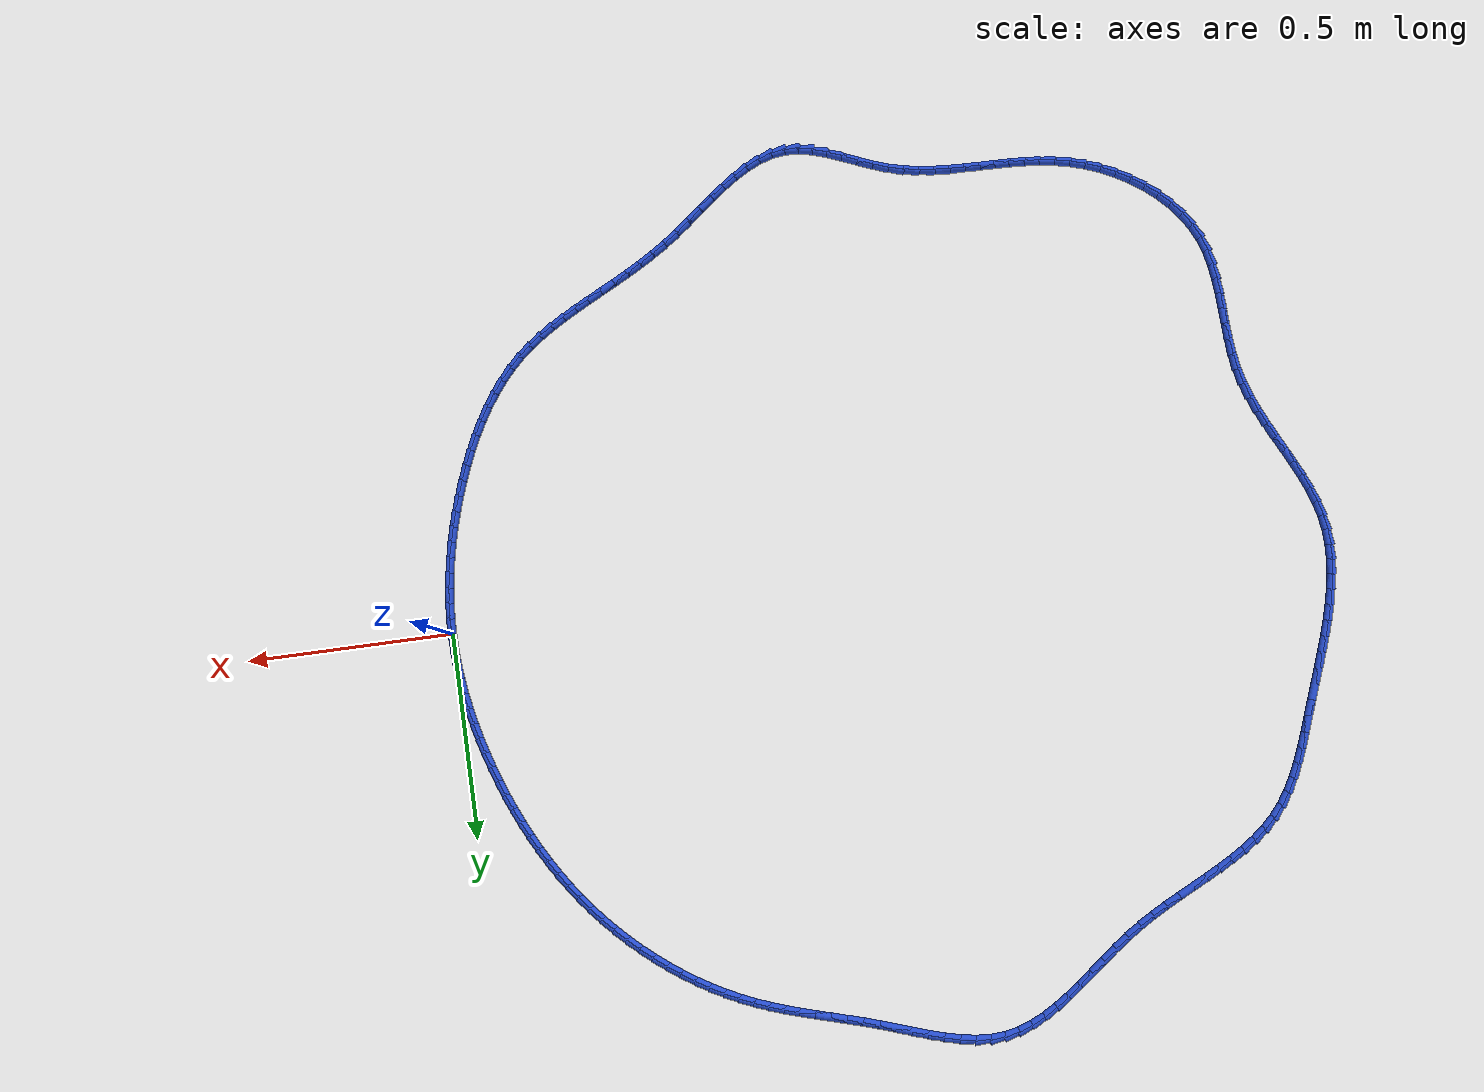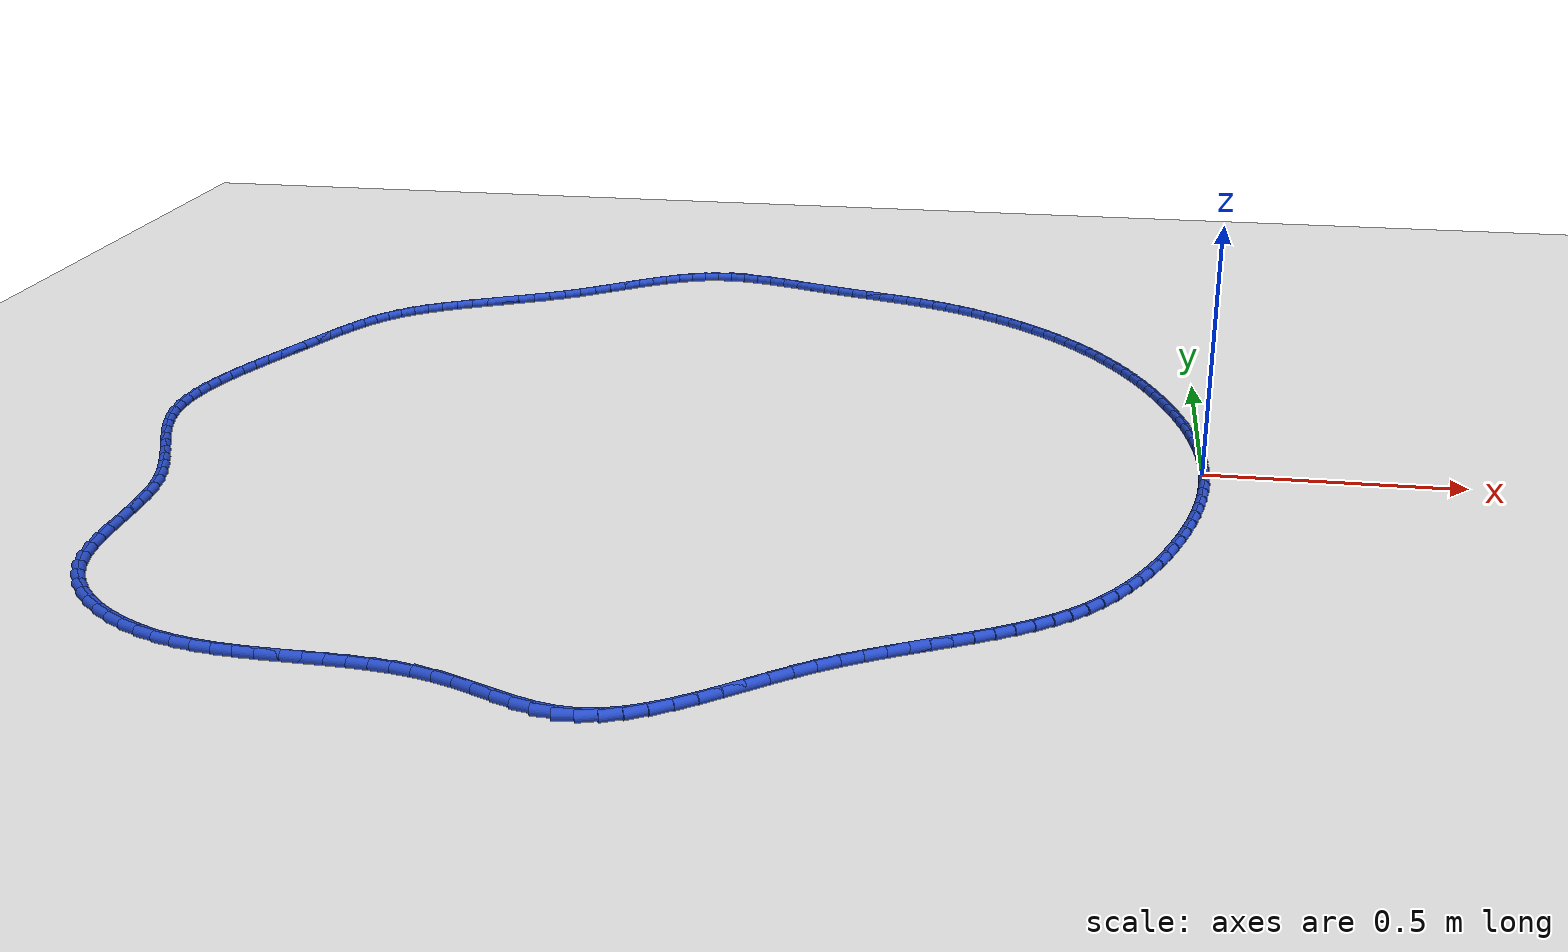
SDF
<sdf version="1.6">
 <world name="default">
  <light name="sun" type="directional">
   <pose>0 0 10 0 -0 0</pose>
   <diffuse>0.8 0.8 0.8 1</diffuse>
   <specular>0.2 0.2 0.2 1</specular>
   <attenuation>
    <range>1000</range>
    <constant>0.9</constant>
    <linear>0.01</linear>
    <quadratic>0.001</quadratic>
   </attenuation>
   <direction>-0.5 0.1 -0.9</direction>
  </light>
  <model name="ground_plane">
   <static>1</static>
   <link name="link">
    <collision name="collision">
     <geometry><plane><normal>0 0 1</normal><size>100 100</size></plane></geometry>
     <surface><friction><ode><mu>100</mu><mu2>50</mu2></ode></friction></surface>
    </collision>
    <visual name="visual">
     <cast_shadows>0</cast_shadows>
     <geometry><plane><normal>0 0 1</normal><size>100 100</size></plane></geometry>
     <material>
      <script><uri>file://media/materials/scripts/gazebo.material</uri><name>Gazebo/WhiteGlow</name></script>
     </material>
    </visual>
   </link>
  </model>
  <gravity>0 0 -9.8</gravity>
  <magnetic_field>6e-06 2.3e-05 -4.2e-05</magnetic_field>
  <atmosphere type="adiabatic"/>
  <physics name="default_physics" default="0" type="ode">
   <max_step_size>0.001</max_step_size>
   <real_time_factor>1</real_time_factor>
   <real_time_update_rate>1000</real_time_update_rate>
  </physics>
  <scene><ambient>0.4 0.4 0.4 1</ambient><background>0.7 0.7 0.7 1</background><shadows>1</shadows></scene>
  <spherical_coordinates>
   <surface_model>EARTH_WGS84</surface_model>
   <latitude_deg>0</latitude_deg>
   <longitude_deg>0</longitude_deg>
   <elevation>0</elevation>
   <heading_deg>0</heading_deg>
  </spherical_coordinates>
  <model name="line">
   <link name="link_0">
    <pose>2.0816681711721685e-17 6.245004513516506e-17 0.01 0 1.57 -1.5462566174582215</pose>
    <collision name="collision">
     <geometry><cylinder><radius>0.01</radius><length>0.08</length></cylinder></geometry>
    </collision>
    <visual name="visual">
     <material>
      <script><name>Gazebo/Blue</name><uri>file://media/materials/scripts/gazebo.material</uri></script>
     </material>
     <geometry><cylinder><radius>0.01</radius><length>0.08</length></cylinder></geometry>
    </visual>
   </link>
   <link name="link_1">
    <pose>-0.0009177256315638624 0.03739006824693077 0.01 0 1.57 -1.5058529207526425</pose>
    <collision name="collision">
     <geometry><cylinder><radius>0.01</radius><length>0.08</length></cylinder></geometry>
    </collision>
    <visual name="visual">
     <material>
      <script><name>Gazebo/Blue</name><uri>file://media/materials/scripts/gazebo.material</uri></script>
     </material>
     <geometry><cylinder><radius>0.01</radius><length>0.08</length></cylinder></geometry>
    </visual>
   </link>
   <link name="link_2">
    <pose>-0.00335029463803867 0.07479414492779995 0.01 0 1.57 -1.4672709662551422</pose>
    <collision name="collision">
     <geometry><cylinder><radius>0.01</radius><length>0.08</length></cylinder></geometry>
    </collision>
    <visual name="visual">
     <material>
      <script><name>Gazebo/Blue</name><uri>file://media/materials/scripts/gazebo.material</uri></script>
     </material>
     <geometry><cylinder><radius>0.01</radius><length>0.08</length></cylinder></geometry>
    </visual>
   </link>
   <link name="link_3">
    <pose>-0.007233058144969507 0.11216549425413652 0.01 0 1.57 -1.430452798421062</pose>
    <collision name="collision">
     <geometry><cylinder><radius>0.01</radius><length>0.08</length></cylinder></geometry>
    </collision>
    <visual name="visual">
     <material>
      <script><name>Gazebo/Blue</name><uri>file://media/materials/scripts/gazebo.material</uri></script>
     </material>
     <geometry><cylinder><radius>0.01</radius><length>0.08</length></cylinder></geometry>
    </visual>
   </link>
   <link name="link_4">
    <pose>-0.012501367277901495 0.1494573804374696 0.01 0 1.57 -1.3953269352057858</pose>
    <collision name="collision">
     <geometry><cylinder><radius>0.01</radius><length>0.08</length></cylinder></geometry>
    </collision>
    <visual name="visual">
     <material>
      <script><name>Gazebo/Blue</name><uri>file://media/materials/scripts/gazebo.material</uri></script>
     </material>
     <geometry><cylinder><radius>0.01</radius><length>0.08</length></cylinder></geometry>
    </visual>
   </link>
   <link name="link_5">
    <pose>-0.019090573162379734 0.18662306768932804 0.01 0 1.57 -1.3618120250505186</pose>
    <collision name="collision">
     <geometry><cylinder><radius>0.01</radius><length>0.08</length></cylinder></geometry>
    </collision>
    <visual name="visual">
     <material>
      <script><name>Gazebo/Blue</name><uri>file://media/materials/scripts/gazebo.material</uri></script>
     </material>
     <geometry><cylinder><radius>0.01</radius><length>0.08</length></cylinder></geometry>
    </visual>
   </link>
   <link name="link_6">
    <pose>-0.026936026923949325 0.22361582022124082 0.01 0 1.57 -1.3298199060829512</pose>
    <collision name="collision">
     <geometry><cylinder><radius>0.01</radius><length>0.08</length></cylinder></geometry>
    </collision>
    <visual name="visual">
     <material>
      <script><name>Gazebo/Blue</name><uri>file://media/materials/scripts/gazebo.material</uri></script>
     </material>
     <geometry><cylinder><radius>0.01</radius><length>0.08</length></cylinder></geometry>
    </visual>
   </link>
   <link name="link_7">
    <pose>-0.035973079688155406 0.26038890224473715 0.01 0 1.57 -1.2992580799029172</pose>
    <collision name="collision">
     <geometry><cylinder><radius>0.01</radius><length>0.08</length></cylinder></geometry>
    </collision>
    <visual name="visual">
     <material>
      <script><name>Gazebo/Blue</name><uri>file://media/materials/scripts/gazebo.material</uri></script>
     </material>
     <geometry><cylinder><radius>0.01</radius><length>0.08</length></cylinder></geometry>
    </visual>
   </link>
   <link name="link_8">
    <pose>-0.04613708258054307 0.29689557797134597 0.01 0 1.57 -1.2700316416066106</pose>
    <collision name="collision">
     <geometry><cylinder><radius>0.01</radius><length>0.08</length></cylinder></geometry>
    </collision>
    <visual name="visual">
     <material>
      <script><name>Gazebo/Blue</name><uri>file://media/materials/scripts/gazebo.material</uri></script>
     </material>
     <geometry><cylinder><radius>0.01</radius><length>0.08</length></cylinder></geometry>
    </visual>
   </link>
   <link name="link_9">
    <pose>-0.05736338672665742 0.333089111612596 0.01 0 1.57 -1.2418852091988863</pose>
    <collision name="collision">
     <geometry><cylinder><radius>0.01</radius><length>0.08</length></cylinder></geometry>
    </collision>
    <visual name="visual">
     <material>
      <script><name>Gazebo/Blue</name><uri>file://media/materials/scripts/gazebo.material</uri></script>
     </material>
     <geometry><cylinder><radius>0.01</radius><length>0.08</length></cylinder></geometry>
    </visual>
   </link>
   <link name="link_10">
    <pose>-0.0695937846546136 0.3689229429635348 0.01 0 1.57 -1.2133597677596022</pose>
    <collision name="collision">
     <geometry><cylinder><radius>0.01</radius><length>0.08</length></cylinder></geometry>
    </collision>
    <visual name="visual">
     <material>
      <script><name>Gazebo/Blue</name><uri>file://media/materials/scripts/gazebo.material</uri></script>
     </material>
     <geometry><cylinder><radius>0.01</radius><length>0.08</length></cylinder></geometry>
    </visual>
   </link>
   <link name="link_11">
    <pose>-0.0828258064759213 0.4043520311468549 0.01 0 1.57 -1.1837099633064239</pose>
    <collision name="collision">
     <geometry><cylinder><radius>0.01</radius><length>0.08</length></cylinder></geometry>
    </collision>
    <visual name="visual">
     <material>
      <script><name>Gazebo/Blue</name><uri>file://media/materials/scripts/gazebo.material</uri></script>
     </material>
     <geometry><cylinder><radius>0.01</radius><length>0.08</length></cylinder></geometry>
    </visual>
   </link>
   <link name="link_12">
    <pose>-0.09708554342652137 0.4393321138210813 0.01 0 1.57 -1.152903792114394</pose>
    <collision name="collision">
     <geometry><cylinder><radius>0.01</radius><length>0.08</length></cylinder></geometry>
    </collision>
    <visual name="visual">
     <material>
      <script><name>Gazebo/Blue</name><uri>file://media/materials/scripts/gazebo.material</uri></script>
     </material>
     <geometry><cylinder><radius>0.01</radius><length>0.08</length></cylinder></geometry>
    </visual>
   </link>
   <link name="link_13">
    <pose>-0.11239931870316211 0.4738189349676631 0.01 0 1.57 -1.1209216302936682</pose>
    <collision name="collision">
     <geometry><cylinder><radius>0.01</radius><length>0.08</length></cylinder></geometry>
    </collision>
    <visual name="visual">
     <material>
      <script><name>Gazebo/Blue</name><uri>file://media/materials/scripts/gazebo.material</uri></script>
     </material>
     <geometry><cylinder><radius>0.01</radius><length>0.08</length></cylinder></geometry>
    </visual>
   </link>
   <link name="link_14">
    <pose>-0.12879345550259177 0.5077682385680489 0.01 0 1.57 -1.0877518998510558</pose>
    <collision name="collision">
     <geometry><cylinder><radius>0.01</radius><length>0.08</length></cylinder></geometry>
    </collision>
    <visual name="visual">
     <material>
      <script><name>Gazebo/Blue</name><uri>file://media/materials/scripts/gazebo.material</uri></script>
     </material>
     <geometry><cylinder><radius>0.01</radius><length>0.08</length></cylinder></geometry>
    </visual>
   </link>
   <link name="link_15">
    <pose>-0.14629427702155862 0.5411357686036876 0.01 0 1.57 -1.0533925577513896</pose>
    <collision name="collision">
     <geometry><cylinder><radius>0.01</radius><length>0.08</length></cylinder></geometry>
    </collision>
    <visual name="visual">
     <material>
      <script><name>Gazebo/Blue</name><uri>file://media/materials/scripts/gazebo.material</uri></script>
     </material>
     <geometry><cylinder><radius>0.01</radius><length>0.08</length></cylinder></geometry>
    </visual>
   </link>
   <link name="link_16">
    <pose>-0.16492810645681089 0.5738772690560279 0.01 0 1.57 -1.0178526163214985</pose>
    <collision name="collision">
     <geometry><cylinder><radius>0.01</radius><length>0.08</length></cylinder></geometry>
    </collision>
    <visual name="visual">
     <material>
      <script><name>Gazebo/Blue</name><uri>file://media/materials/scripts/gazebo.material</uri></script>
     </material>
     <geometry><cylinder><radius>0.01</radius><length>0.08</length></cylinder></geometry>
    </visual>
   </link>
   <link name="link_17">
    <pose>-0.1847212670050968 0.6059484839065186 0.01 0 1.57 -0.9811536308472887</pose>
    <collision name="collision">
     <geometry><cylinder><radius>0.01</radius><length>0.08</length></cylinder></geometry>
    </collision>
    <visual name="visual">
     <material>
      <script><name>Gazebo/Blue</name><uri>file://media/materials/scripts/gazebo.material</uri></script>
     </material>
     <geometry><cylinder><radius>0.01</radius><length>0.08</length></cylinder></geometry>
    </visual>
   </link>
   <link name="link_18">
    <pose>-0.2057000818631647 0.6373051571366083 0.01 0 1.57 -0.9433310739540354</pose>
    <collision name="collision">
     <geometry><cylinder><radius>0.01</radius><length>0.08</length></cylinder></geometry>
    </collision>
    <visual name="visual">
     <material>
      <script><name>Gazebo/Blue</name><uri>file://media/materials/scripts/gazebo.material</uri></script>
     </material>
     <geometry><cylinder><radius>0.01</radius><length>0.08</length></cylinder></geometry>
    </visual>
   </link>
   <link name="link_19">
    <pose>-0.22789087422776277 0.6679030327277459 0.01 0 1.57 -0.9044359164735142</pose>
    <collision name="collision">
     <geometry><cylinder><radius>0.01</radius><length>0.08</length></cylinder></geometry>
    </collision>
    <visual name="visual">
     <material>
      <script><name>Gazebo/Blue</name><uri>file://media/materials/scripts/gazebo.material</uri></script>
     </material>
     <geometry><cylinder><radius>0.01</radius><length>0.08</length></cylinder></geometry>
    </visual>
   </link>
   <link name="link_20">
    <pose>-0.2513199418789945 0.6976978477420025 0.01 0 1.57 -0.8648703252236555</pose>
    <collision name="collision">
     <geometry><cylinder><radius>0.01</radius><length>0.08</length></cylinder></geometry>
    </collision>
    <visual name="visual">
     <material>
      <script><name>Gazebo/Blue</name><uri>file://media/materials/scripts/gazebo.material</uri></script>
     </material>
     <geometry><cylinder><radius>0.01</radius><length>0.08</length></cylinder></geometry>
    </visual>
   </link>
   <link name="link_21">
    <pose>-0.2759917229875353 0.7266393882241484 0.01 0 1.57 -0.8255422555683686</pose>
    <collision name="collision">
     <geometry><cylinder><radius>0.01</radius><length>0.08</length></cylinder></geometry>
    </collision>
    <visual name="visual">
     <material>
      <script><name>Gazebo/Blue</name><uri>file://media/materials/scripts/gazebo.material</uri></script>
     </material>
     <geometry><cylinder><radius>0.01</radius><length>0.08</length></cylinder></geometry>
    </visual>
   </link>
   <link name="link_22">
    <pose>-0.30184889996766184 0.7546606279526599 0.01 0 1.57 -0.786445059237418</pose>
    <collision name="collision">
     <geometry><cylinder><radius>0.01</radius><length>0.08</length></cylinder></geometry>
    </collision>
    <visual name="visual">
     <material>
      <script><name>Gazebo/Blue</name><uri>file://media/materials/scripts/gazebo.material</uri></script>
     </material>
     <geometry><cylinder><radius>0.01</radius><length>0.08</length></cylinder></geometry>
    </visual>
   </link>
   <link name="link_23">
    <pose>-0.3288233267573326 0.7816915927828084 0.01 0 1.57 -0.747397326956661</pose>
    <collision name="collision">
     <geometry><cylinder><radius>0.01</radius><length>0.08</length></cylinder></geometry>
    </collision>
    <visual name="visual">
     <material>
      <script><name>Gazebo/Blue</name><uri>file://media/materials/scripts/gazebo.material</uri></script>
     </material>
     <geometry><cylinder><radius>0.01</radius><length>0.08</length></cylinder></geometry>
    </visual>
   </link>
   <link name="link_24">
    <pose>-0.3568468572945061 0.8076623085698642 0.01 0 1.57 -0.7082187413780048</pose>
    <collision name="collision">
     <geometry><cylinder><radius>0.01</radius><length>0.08</length></cylinder></geometry>
    </collision>
    <visual name="visual">
     <material>
      <script><name>Gazebo/Blue</name><uri>file://media/materials/scripts/gazebo.material</uri></script>
     </material>
     <geometry><cylinder><radius>0.01</radius><length>0.08</length></cylinder></geometry>
    </visual>
   </link>
   <link name="link_25">
    <pose>-0.3858513455171411 0.8325028011690981 0.01 0 1.57 -0.6687293947517815</pose>
    <collision name="collision">
     <geometry><cylinder><radius>0.01</radius><length>0.08</length></cylinder></geometry>
    </collision>
    <visual name="visual">
     <material>
      <script><name>Gazebo/Blue</name><uri>file://media/materials/scripts/gazebo.material</uri></script>
     </material>
     <geometry><cylinder><radius>0.01</radius><length>0.08</length></cylinder></geometry>
    </visual>
   </link>
   <link name="link_26">
    <pose>-0.41576864536319624 0.8561430964357809 0.01 0 1.57 -0.6287491965845003</pose>
    <collision name="collision">
     <geometry><cylinder><radius>0.01</radius><length>0.08</length></cylinder></geometry>
    </collision>
    <visual name="visual">
     <material>
      <script><name>Gazebo/Blue</name><uri>file://media/materials/scripts/gazebo.material</uri></script>
     </material>
     <geometry><cylinder><radius>0.01</radius><length>0.08</length></cylinder></geometry>
    </visual>
   </link>
   <link name="link_27">
    <pose>-0.4465306107706297 0.8785132202251827 0.01 0 1.57 -0.5880974610533554</pose>
    <collision name="collision">
     <geometry><cylinder><radius>0.01</radius><length>0.08</length></cylinder></geometry>
    </collision>
    <visual name="visual">
     <material>
      <script><name>Gazebo/Blue</name><uri>file://media/materials/scripts/gazebo.material</uri></script>
     </material>
     <geometry><cylinder><radius>0.01</radius><length>0.08</length></cylinder></geometry>
    </visual>
   </link>
   <link name="link_28">
    <pose>-0.4780690956774006 0.8995431983925747 0.01 0 1.57 -0.5465927741109644</pose>
    <collision name="collision">
     <geometry><cylinder><radius>0.01</radius><length>0.08</length></cylinder></geometry>
    </collision>
    <visual name="visual">
     <material>
      <script><name>Gazebo/Blue</name><uri>file://media/materials/scripts/gazebo.material</uri></script>
     </material>
     <geometry><cylinder><radius>0.01</radius><length>0.08</length></cylinder></geometry>
    </visual>
   </link>
   <link name="link_29">
    <pose>-0.5103159540214676 0.919163056793228 0.01 0 1.57 -0.5040532559833172</pose>
    <collision name="collision">
     <geometry><cylinder><radius>0.01</radius><length>0.08</length></cylinder></geometry>
    </collision>
    <visual name="visual">
     <material>
      <script><name>Gazebo/Blue</name><uri>file://media/materials/scripts/gazebo.material</uri></script>
     </material>
     <geometry><cylinder><radius>0.01</radius><length>0.08</length></cylinder></geometry>
    </visual>
   </link>
   <link name="link_30">
    <pose>-0.5432030397407889 0.9373028212824126 0.01 0 1.57 -0.46029735492171425</pose>
    <collision name="collision">
     <geometry><cylinder><radius>0.01</radius><length>0.08</length></cylinder></geometry>
    </collision>
    <visual name="visual">
     <material>
      <script><name>Gazebo/Blue</name><uri>file://media/materials/scripts/gazebo.material</uri></script>
     </material>
     <geometry><cylinder><radius>0.01</radius><length>0.08</length></cylinder></geometry>
    </visual>
   </link>
   <link name="link_31">
    <pose>-0.5766622067733229 0.9538925177153991 0.01 0 1.57 -0.41520308218590973</pose>
    <collision name="collision">
     <geometry><cylinder><radius>0.01</radius><length>0.08</length></cylinder></geometry>
    </collision>
    <visual name="visual">
     <material>
      <script><name>Gazebo/Blue</name><uri>file://media/materials/scripts/gazebo.material</uri></script>
     </material>
     <geometry><cylinder><radius>0.01</radius><length>0.08</length></cylinder></geometry>
    </visual>
   </link>
   <link name="link_32">
    <pose>-0.6106256139430398 0.9688646488899402 0.01 0 1.57 -0.3721206774624496</pose>
    <collision name="collision">
     <geometry><cylinder><radius>0.01</radius><length>0.08</length></cylinder></geometry>
    </collision>
    <visual name="visual">
     <material>
      <script><name>Gazebo/Blue</name><uri>file://media/materials/scripts/gazebo.material</uri></script>
     </material>
     <geometry><cylinder><radius>0.01</radius><length>0.08</length></cylinder></geometry>
    </visual>
   </link>
   <link name="link_33">
    <pose>-0.6450434374206725 0.9822980933967411 0.01 0 1.57 -0.3367176333923286</pose>
    <collision name="collision">
     <geometry><cylinder><radius>0.01</radius><length>0.08</length></cylinder></geometry>
    </collision>
    <visual name="visual">
     <material>
      <script><name>Gazebo/Blue</name><uri>file://media/materials/scripts/gazebo.material</uri></script>
     </material>
     <geometry><cylinder><radius>0.01</radius><length>0.08</length></cylinder></geometry>
    </visual>
   </link>
   <link name="link_34">
    <pose>-0.6798936228155037 0.9944973331653777 0.01 0 1.57 -0.30982278114631934</pose>
    <collision name="collision">
     <geometry><cylinder><radius>0.01</radius><length>0.08</length></cylinder></geometry>
    </collision>
    <visual name="visual">
     <material>
      <script><name>Gazebo/Blue</name><uri>file://media/materials/scripts/gazebo.material</uri></script>
     </material>
     <geometry><cylinder><radius>0.01</radius><length>0.08</length></cylinder></geometry>
    </visual>
   </link>
   <link name="link_35">
    <pose>-0.7151564861978593 1.005786108128249 0.01 0 1.57 -0.2915929750230903</pose>
    <collision name="collision">
     <geometry><cylinder><radius>0.01</radius><length>0.08</length></cylinder></geometry>
    </collision>
    <visual name="visual">
     <material>
      <script><name>Gazebo/Blue</name><uri>file://media/materials/scripts/gazebo.material</uri></script>
     </material>
     <geometry><cylinder><radius>0.01</radius><length>0.08</length></cylinder></geometry>
    </visual>
   </link>
   <link name="link_36">
    <pose>-0.7508123436380649 1.016488158217755 0.01 0 1.57 -0.28201691279708313</pose>
    <collision name="collision">
     <geometry><cylinder><radius>0.01</radius><length>0.08</length></cylinder></geometry>
    </collision>
    <visual name="visual">
     <material>
      <script><name>Gazebo/Blue</name><uri>file://media/materials/scripts/gazebo.material</uri></script>
     </material>
     <geometry><cylinder><radius>0.01</radius><length>0.08</length></cylinder></geometry>
    </visual>
   </link>
   <link name="link_37">
    <pose>-0.7868415112064465 1.0269272233662947 0.01 0 1.57 -0.2809590969551456</pose>
    <collision name="collision">
     <geometry><cylinder><radius>0.01</radius><length>0.08</length></cylinder></geometry>
    </collision>
    <visual name="visual">
     <material>
      <script><name>Gazebo/Blue</name><uri>file://media/materials/scripts/gazebo.material</uri></script>
     </material>
     <geometry><cylinder><radius>0.01</radius><length>0.08</length></cylinder></geometry>
    </visual>
   </link>
   <link name="link_38">
    <pose>-0.8232243049733294 1.0374270435062667 0.01 0 1.57 -0.28818769384749265</pose>
    <collision name="collision">
     <geometry><cylinder><radius>0.01</radius><length>0.08</length></cylinder></geometry>
    </collision>
    <visual name="visual">
     <material>
      <script><name>Gazebo/Blue</name><uri>file://media/materials/scripts/gazebo.material</uri></script>
     </material>
     <geometry><cylinder><radius>0.01</radius><length>0.08</length></cylinder></geometry>
    </visual>
   </link>
   <link name="link_39">
    <pose>-0.8599410410090392 1.0483113585700705 0.01 0 1.57 -0.30338578694096824</pose>
    <collision name="collision">
     <geometry><cylinder><radius>0.01</radius><length>0.08</length></cylinder></geometry>
    </collision>
    <visual name="visual">
     <material>
      <script><name>Gazebo/Blue</name><uri>file://media/materials/scripts/gazebo.material</uri></script>
     </material>
     <geometry><cylinder><radius>0.01</radius><length>0.08</length></cylinder></geometry>
    </visual>
   </link>
   <link name="link_40">
    <pose>-0.8969720353839028 1.0599039084901065 0.01 0 1.57 -0.3231190863596062</pose>
    <collision name="collision">
     <geometry><cylinder><radius>0.01</radius><length>0.08</length></cylinder></geometry>
    </collision>
    <visual name="visual">
     <material>
      <script><name>Gazebo/Blue</name><uri>file://media/materials/scripts/gazebo.material</uri></script>
     </material>
     <geometry><cylinder><radius>0.01</radius><length>0.08</length></cylinder></geometry>
    </visual>
   </link>
   <link name="link_41">
    <pose>-0.9342801258253346 1.0723966949127712 0.01 0 1.57 -0.33053541534569847</pose>
    <collision name="collision">
     <geometry><cylinder><radius>0.01</radius><length>0.08</length></cylinder></geometry>
    </collision>
    <visual name="visual">
     <material>
      <script><name>Gazebo/Blue</name><uri>file://media/materials/scripts/gazebo.material</uri></script>
     </material>
     <geometry><cylinder><radius>0.01</radius><length>0.08</length></cylinder></geometry>
    </visual>
   </link>
   <link name="link_42">
    <pose>-0.9717306499767384 1.0852468389515075 0.01 0 1.57 -0.3201882021681557</pose>
    <collision name="collision">
     <geometry><cylinder><radius>0.01</radius><length>0.08</length></cylinder></geometry>
    </collision>
    <visual name="visual">
     <material>
      <script><name>Gazebo/Blue</name><uri>file://media/materials/scripts/gazebo.material</uri></script>
     </material>
     <geometry><cylinder><radius>0.01</radius><length>0.08</length></cylinder></geometry>
    </visual>
   </link>
   <link name="link_43">
    <pose>-1.0091551502357876 1.097656739188548 0.01 0 1.57 -0.2915260342607785</pose>
    <collision name="collision">
     <geometry><cylinder><radius>0.01</radius><length>0.08</length></cylinder></geometry>
    </collision>
    <visual name="visual">
     <material>
      <script><name>Gazebo/Blue</name><uri>file://media/materials/scripts/gazebo.material</uri></script>
     </material>
     <geometry><cylinder><radius>0.01</radius><length>0.08</length></cylinder></geometry>
    </visual>
   </link>
   <link name="link_44">
    <pose>-1.0463851359029452 1.1088285447448425 0.01 0 1.57 -0.242912685368722</pose>
    <collision name="collision">
     <geometry><cylinder><radius>0.01</radius><length>0.08</length></cylinder></geometry>
    </collision>
    <visual name="visual">
     <material>
      <script><name>Gazebo/Blue</name><uri>file://media/materials/scripts/gazebo.material</uri></script>
     </material>
     <geometry><cylinder><radius>0.01</radius><length>0.08</length></cylinder></geometry>
    </visual>
   </link>
   <link name="link_45">
    <pose>-1.0832521162786735 1.1179644047413402 0.01 0 1.57 -0.17173261437466977</pose>
    <collision name="collision">
     <geometry><cylinder><radius>0.01</radius><length>0.08</length></cylinder></geometry>
    </collision>
    <visual name="visual">
     <material>
      <script><name>Gazebo/Blue</name><uri>file://media/materials/scripts/gazebo.material</uri></script>
     </material>
     <geometry><cylinder><radius>0.01</radius><length>0.08</length></cylinder></geometry>
    </visual>
   </link>
   <link name="link_46">
    <pose>-1.1195876006634353 1.124266468298991 0.01 0 1.57 -0.07479717048199354</pose>
    <collision name="collision">
     <geometry><cylinder><radius>0.01</radius><length>0.08</length></cylinder></geometry>
    </collision>
    <visual name="visual">
     <material>
      <script><name>Gazebo/Blue</name><uri>file://media/materials/scripts/gazebo.material</uri></script>
     </material>
     <geometry><cylinder><radius>0.01</radius><length>0.08</length></cylinder></geometry>
    </visual>
   </link>
   <link name="link_47">
    <pose>-1.1552230983576937 1.1269368845387442 0.01 0 1.57 0.05055013611710461</pose>
    <collision name="collision">
     <geometry><cylinder><radius>0.01</radius><length>0.08</length></cylinder></geometry>
    </collision>
    <visual name="visual">
     <material>
      <script><name>Gazebo/Blue</name><uri>file://media/materials/scripts/gazebo.material</uri></script>
     </material>
     <geometry><cylinder><radius>0.01</radius><length>0.08</length></cylinder></geometry>
    </visual>
   </link>
   <link name="link_48">
    <pose>-1.1899901438676448 1.125177907152692 0.01 0 1.57 0.19527162372627327</pose>
    <collision name="collision">
     <geometry><cylinder><radius>0.01</radius><length>0.08</length></cylinder></geometry>
    </collision>
    <visual name="visual">
     <material>
      <script><name>Gazebo/Blue</name><uri>file://media/materials/scripts/gazebo.material</uri></script>
     </material>
     <geometry><cylinder><radius>0.01</radius><length>0.08</length></cylinder></geometry>
    </visual>
   </link>
   <link name="link_49">
    <pose>-1.2237926441244469 1.1184920416351813 0.01 0 1.57 0.3261358950479793</pose>
    <collision name="collision">
     <geometry><cylinder><radius>0.01</radius><length>0.08</length></cylinder></geometry>
    </collision>
    <visual name="visual">
     <material>
      <script><name>Gazebo/Blue</name><uri>file://media/materials/scripts/gazebo.material</uri></script>
     </material>
     <geometry><cylinder><radius>0.01</radius><length>0.08</length></cylinder></geometry>
    </visual>
   </link>
   <link name="link_50">
    <pose>-1.256765515781614 1.1073401845461448 0.01 0 1.57 0.4336134931897716</pose>
    <collision name="collision">
     <geometry><cylinder><radius>0.01</radius><length>0.08</length></cylinder></geometry>
    </collision>
    <visual name="visual">
     <material>
      <script><name>Gazebo/Blue</name><uri>file://media/materials/scripts/gazebo.material</uri></script>
     </material>
     <geometry><cylinder><radius>0.01</radius><length>0.08</length></cylinder></geometry>
    </visual>
   </link>
   <link name="link_51">
    <pose>-1.289089668225055 1.0923740426995454 0.01 0 1.57 0.5173717828774678</pose>
    <collision name="collision">
     <geometry><cylinder><radius>0.01</radius><length>0.08</length></cylinder></geometry>
    </collision>
    <visual name="visual">
     <material>
      <script><name>Gazebo/Blue</name><uri>file://media/materials/scripts/gazebo.material</uri></script>
     </material>
     <geometry><cylinder><radius>0.01</radius><length>0.08</length></cylinder></geometry>
    </visual>
   </link>
   <link name="link_52">
    <pose>-1.3209460108406779 1.0742453229093474 0.01 0 1.57 0.5790306114568059</pose>
    <collision name="collision">
     <geometry><cylinder><radius>0.01</radius><length>0.08</length></cylinder></geometry>
    </collision>
    <visual name="visual">
     <material>
      <script><name>Gazebo/Blue</name><uri>file://media/materials/scripts/gazebo.material</uri></script>
     </material>
     <geometry><cylinder><radius>0.01</radius><length>0.08</length></cylinder></geometry>
    </visual>
   </link>
   <link name="link_53">
    <pose>-1.3525154530143901 1.0536057319895147 0.01 0 1.57 0.6207725133455624</pose>
    <collision name="collision">
     <geometry><cylinder><radius>0.01</radius><length>0.08</length></cylinder></geometry>
    </collision>
    <visual name="visual">
     <material>
      <script><name>Gazebo/Blue</name><uri>file://media/materials/scripts/gazebo.material</uri></script>
     </material>
     <geometry><cylinder><radius>0.01</radius><length>0.08</length></cylinder></geometry>
    </visual>
   </link>
   <link name="link_54">
    <pose>-1.3839789041320998 1.0311069767540115 0.01 0 1.57 0.6445643230539471</pose>
    <collision name="collision">
     <geometry><cylinder><radius>0.01</radius><length>0.08</length></cylinder></geometry>
    </collision>
    <visual name="visual">
     <material>
      <script><name>Gazebo/Blue</name><uri>file://media/materials/scripts/gazebo.material</uri></script>
     </material>
     <geometry><cylinder><radius>0.01</radius><length>0.08</length></cylinder></geometry>
    </visual>
   </link>
   <link name="link_55">
    <pose>-1.415517273579715 1.0074007640168008 0.01 0 1.57 0.6518287813514151</pose>
    <collision name="collision">
     <geometry><cylinder><radius>0.01</radius><length>0.08</length></cylinder></geometry>
    </collision>
    <visual name="visual">
     <material>
      <script><name>Gazebo/Blue</name><uri>file://media/materials/scripts/gazebo.material</uri></script>
     </material>
     <geometry><cylinder><radius>0.01</radius><length>0.08</length></cylinder></geometry>
    </visual>
   </link>
   <link name="link_56">
    <pose>-1.4473114707431436 0.983138800591848 0.01 0 1.57 0.6433582563006961</pose>
    <collision name="collision">
     <geometry><cylinder><radius>0.01</radius><length>0.08</length></cylinder></geometry>
    </collision>
    <visual name="visual">
     <material>
      <script><name>Gazebo/Blue</name><uri>file://media/materials/scripts/gazebo.material</uri></script>
     </material>
     <geometry><cylinder><radius>0.01</radius><length>0.08</length></cylinder></geometry>
    </visual>
   </link>
   <link name="link_57">
    <pose>-1.4795424050082941 0.9589727932931161 0.01 0 1.57 0.619343248630212</pose>
    <collision name="collision">
     <geometry><cylinder><radius>0.01</radius><length>0.08</length></cylinder></geometry>
    </collision>
    <visual name="visual">
     <material>
      <script><name>Gazebo/Blue</name><uri>file://media/materials/scripts/gazebo.material</uri></script>
     </material>
     <geometry><cylinder><radius>0.01</radius><length>0.08</length></cylinder></geometry>
    </visual>
   </link>
   <link name="link_58">
    <pose>-1.5123909857610744 0.9355544489345692 0.01 0 1.57 0.5795523622698867</pose>
    <collision name="collision">
     <geometry><cylinder><radius>0.01</radius><length>0.08</length></cylinder></geometry>
    </collision>
    <visual name="visual">
     <material>
      <script><name>Gazebo/Blue</name><uri>file://media/materials/scripts/gazebo.material</uri></script>
     </material>
     <geometry><cylinder><radius>0.01</radius><length>0.08</length></cylinder></geometry>
    </visual>
   </link>
   <link name="link_59">
    <pose>-1.54603665686944 0.9135323864492655 0.01 0 1.57 0.532619440617861</pose>
    <collision name="collision">
     <geometry><cylinder><radius>0.01</radius><length>0.08</length></cylinder></geometry>
    </collision>
    <visual name="visual">
     <material>
      <script><name>Gazebo/Blue</name><uri>file://media/materials/scripts/gazebo.material</uri></script>
     </material>
     <geometry><cylinder><radius>0.01</radius><length>0.08</length></cylinder></geometry>
    </visual>
   </link>
   <link name="link_60">
    <pose>-1.5804991753977038 0.8932187609069488 0.01 0 1.57 0.49576252603368226</pose>
    <collision name="collision">
     <geometry><cylinder><radius>0.01</radius><length>0.08</length></cylinder></geometry>
    </collision>
    <visual name="visual">
     <material>
      <script><name>Gazebo/Blue</name><uri>file://media/materials/scripts/gazebo.material</uri></script>
     </material>
     <geometry><cylinder><radius>0.01</radius><length>0.08</length></cylinder></geometry>
    </visual>
   </link>
   <link name="link_61">
    <pose>-1.6154972253749693 0.874291359387935 0.01 0 1.57 0.4709852755989723</pose>
    <collision name="collision">
     <geometry><cylinder><radius>0.01</radius><length>0.08</length></cylinder></geometry>
    </collision>
    <visual name="visual">
     <material>
      <script><name>Gazebo/Blue</name><uri>file://media/materials/scripts/gazebo.material</uri></script>
     </material>
     <geometry><cylinder><radius>0.01</radius><length>0.08</length></cylinder></geometry>
    </visual>
   </link>
   <link name="link_62">
    <pose>-1.6507161315610732 0.8563576802050316 0.01 0 1.57 0.45839353250777737</pose>
    <collision name="collision">
     <geometry><cylinder><radius>0.01</radius><length>0.08</length></cylinder></geometry>
    </collision>
    <visual name="visual">
     <material>
      <script><name>Gazebo/Blue</name><uri>file://media/materials/scripts/gazebo.material</uri></script>
     </material>
     <geometry><cylinder><radius>0.01</radius><length>0.08</length></cylinder></geometry>
    </visual>
   </link>
   <link name="link_63">
    <pose>-1.685841218715853 0.8390252216710464 0.01 0 1.57 0.4582279485417565</pose>
    <collision name="collision">
     <geometry><cylinder><radius>0.01</radius><length>0.08</length></cylinder></geometry>
    </collision>
    <visual name="visual">
     <material>
      <script><name>Gazebo/Blue</name><uri>file://media/materials/scripts/gazebo.material</uri></script>
     </material>
     <geometry><cylinder><radius>0.01</radius><length>0.08</length></cylinder></geometry>
    </visual>
   </link>
   <link name="link_64">
    <pose>-1.7205578115991433 0.821901482098788 0.01 0 1.57 0.47093543146204925</pose>
    <collision name="collision">
     <geometry><cylinder><radius>0.01</radius><length>0.08</length></cylinder></geometry>
    </collision>
    <visual name="visual">
     <material>
      <script><name>Gazebo/Blue</name><uri>file://media/materials/scripts/gazebo.material</uri></script>
     </material>
     <geometry><cylinder><radius>0.01</radius><length>0.08</length></cylinder></geometry>
    </visual>
   </link>
   <link name="link_65">
    <pose>-1.7545512349707815 0.8045939598010642 0.01 0 1.57 0.49719353786730586</pose>
    <collision name="collision">
     <geometry><cylinder><radius>0.01</radius><length>0.08</length></cylinder></geometry>
    </collision>
    <visual name="visual">
     <material>
      <script><name>Gazebo/Blue</name><uri>file://media/materials/scripts/gazebo.material</uri></script>
     </material>
     <geometry><cylinder><radius>0.01</radius><length>0.08</length></cylinder></geometry>
    </visual>
   </link>
   <link name="link_66">
    <pose>-1.787506813590604 0.7867101530906826 0.01 0 1.57 0.5378739308355532</pose>
    <collision name="collision">
     <geometry><cylinder><radius>0.01</radius><length>0.08</length></cylinder></geometry>
    </collision>
    <visual name="visual">
     <material>
      <script><name>Gazebo/Blue</name><uri>file://media/materials/scripts/gazebo.material</uri></script>
     </material>
     <geometry><cylinder><radius>0.01</radius><length>0.08</length></cylinder></geometry>
    </visual>
   </link>
   <link name="link_67">
    <pose>-1.8191098722184462 0.7678575602804519 0.01 0 1.57 0.5939142552099661</pose>
    <collision name="collision">
     <geometry><cylinder><radius>0.01</radius><length>0.08</length></cylinder></geometry>
    </collision>
    <visual name="visual">
     <material>
      <script><name>Gazebo/Blue</name><uri>file://media/materials/scripts/gazebo.material</uri></script>
     </material>
     <geometry><cylinder><radius>0.01</radius><length>0.08</length></cylinder></geometry>
    </visual>
   </link>
   <link name="link_68">
    <pose>-1.849045735614145 0.7476436796831796 0.01 0 1.57 0.6660536904923708</pose>
    <collision name="collision">
     <geometry><cylinder><radius>0.01</radius><length>0.08</length></cylinder></geometry>
    </collision>
    <visual name="visual">
     <material>
      <script><name>Gazebo/Blue</name><uri>file://media/materials/scripts/gazebo.material</uri></script>
     </material>
     <geometry><cylinder><radius>0.01</radius><length>0.08</length></cylinder></geometry>
    </visual>
   </link>
   <link name="link_69">
    <pose>-1.876999728537537 0.7256760096116738 0.01 0 1.57 0.7543966001571656</pose>
    <collision name="collision">
     <geometry><cylinder><radius>0.01</radius><length>0.08</length></cylinder></geometry>
    </collision>
    <visual name="visual">
     <material>
      <script><name>Gazebo/Blue</name><uri>file://media/materials/scripts/gazebo.material</uri></script>
     </material>
     <geometry><cylinder><radius>0.01</radius><length>0.08</length></cylinder></geometry>
    </visual>
   </link>
   <link name="link_70">
    <pose>-1.9026571757484587 0.7015620483787428 0.01 0 1.57 0.8575896992110907</pose>
    <collision name="collision">
     <geometry><cylinder><radius>0.01</radius><length>0.08</length></cylinder></geometry>
    </collision>
    <visual name="visual">
     <material>
      <script><name>Gazebo/Blue</name><uri>file://media/materials/scripts/gazebo.material</uri></script>
     </material>
     <geometry><cylinder><radius>0.01</radius><length>0.08</length></cylinder></geometry>
    </visual>
   </link>
   <link name="link_71">
    <pose>-1.9257095980576204 0.674915537944913 0.01 0 1.57 0.9611003623769234</pose>
    <collision name="collision">
     <geometry><cylinder><radius>0.01</radius><length>0.08</length></cylinder></geometry>
    </collision>
    <visual name="visual">
     <material>
      <script><name>Gazebo/Blue</name><uri>file://media/materials/scripts/gazebo.material</uri></script>
     </material>
     <geometry><cylinder><radius>0.01</radius><length>0.08</length></cylinder></geometry>
    </visual>
   </link>
   <link name="link_72">
    <pose>-1.9461487001970428 0.645652710145892 0.01 0 1.57 1.046221841648937</pose>
    <collision name="collision">
     <geometry><cylinder><radius>0.01</radius><length>0.08</length></cylinder></geometry>
    </collision>
    <visual name="visual">
     <material>
      <script><name>Gazebo/Blue</name><uri>file://media/materials/scripts/gazebo.material</uri></script>
     </material>
     <geometry><cylinder><radius>0.01</radius><length>0.08</length></cylinder></geometry>
    </visual>
   </link>
   <link name="link_73">
    <pose>-1.9643944078938174 0.6141213073219528 0.01 0 1.57 1.112056601688501</pose>
    <collision name="collision">
     <geometry><cylinder><radius>0.01</radius><length>0.08</length></cylinder></geometry>
    </collision>
    <visual name="visual">
     <material>
      <script><name>Gazebo/Blue</name><uri>file://media/materials/scripts/gazebo.material</uri></script>
     </material>
     <geometry><cylinder><radius>0.01</radius><length>0.08</length></cylinder></geometry>
    </visual>
   </link>
   <link name="link_74">
    <pose>-1.9808994677024254 0.5807021447639038 0.01 0 1.57 1.1599012246335134</pose>
    <collision name="collision">
     <geometry><cylinder><radius>0.01</radius><length>0.08</length></cylinder></geometry>
    </collision>
    <visual name="visual">
     <material>
      <script><name>Gazebo/Blue</name><uri>file://media/materials/scripts/gazebo.material</uri></script>
     </material>
     <geometry><cylinder><radius>0.01</radius><length>0.08</length></cylinder></geometry>
    </visual>
   </link>
   <link name="link_75">
    <pose>-1.9961166261773498 0.5457760377625546 0.01 0 1.57 1.191220238394075</pose>
    <collision name="collision">
     <geometry><cylinder><radius>0.01</radius><length>0.08</length></cylinder></geometry>
    </collision>
    <visual name="visual">
     <material>
      <script><name>Gazebo/Blue</name><uri>file://media/materials/scripts/gazebo.material</uri></script>
     </material>
     <geometry><cylinder><radius>0.01</radius><length>0.08</length></cylinder></geometry>
    </visual>
   </link>
   <link name="link_76">
    <pose>-2.010498629873072 0.5097238016087139 0.01 0 1.57 1.2072569263946782</pose>
    <collision name="collision">
     <geometry><cylinder><radius>0.01</radius><length>0.08</length></cylinder></geometry>
    </collision>
    <visual name="visual">
     <material>
      <script><name>Gazebo/Blue</name><uri>file://media/materials/scripts/gazebo.material</uri></script>
     </material>
     <geometry><cylinder><radius>0.01</radius><length>0.08</length></cylinder></geometry>
    </visual>
   </link>
   <link name="link_77">
    <pose>-2.0244982253440744 0.4729262515931899 0.01 0 1.57 1.2088927748744391</pose>
    <collision name="collision">
     <geometry><cylinder><radius>0.01</radius><length>0.08</length></cylinder></geometry>
    </collision>
    <visual name="visual">
     <material>
      <script><name>Gazebo/Blue</name><uri>file://media/materials/scripts/gazebo.material</uri></script>
     </material>
     <geometry><cylinder><radius>0.01</radius><length>0.08</length></cylinder></geometry>
    </visual>
   </link>
   <link name="link_78">
    <pose>-2.0385671149823406 0.43576375839859477 0.01 0 1.57 1.2026971861670386</pose>
    <collision name="collision">
     <geometry><cylinder><radius>0.01</radius><length>0.08</length></cylinder></geometry>
    </collision>
    <visual name="visual">
     <material>
      <script><name>Gazebo/Blue</name><uri>file://media/materials/scripts/gazebo.material</uri></script>
     </material>
     <geometry><cylinder><radius>0.01</radius><length>0.08</length></cylinder></geometry>
    </visual>
   </link>
   <link name="link_79">
    <pose>-2.0529310289638207 0.39852047291427833 0.01 0 1.57 1.2024738995685083</pose>
    <collision name="collision">
     <geometry><cylinder><radius>0.01</radius><length>0.08</length></cylinder></geometry>
    </collision>
    <visual name="visual">
     <material>
      <script><name>Gazebo/Blue</name><uri>file://media/materials/scripts/gazebo.material</uri></script>
     </material>
     <geometry><cylinder><radius>0.01</radius><length>0.08</length></cylinder></geometry>
    </visual>
   </link>
   <link name="link_80">
    <pose>-2.067309240770012 0.3612648949230466 0.01 0 1.57 1.210092759810846</pose>
    <collision name="collision">
     <geometry><cylinder><radius>0.01</radius><length>0.08</length></cylinder></geometry>
    </collision>
    <visual name="visual">
     <material>
      <script><name>Gazebo/Blue</name><uri>file://media/materials/scripts/gazebo.material</uri></script>
     </material>
     <geometry><cylinder><radius>0.01</radius><length>0.08</length></cylinder></geometry>
    </visual>
   </link>
   <link name="link_81">
    <pose>-2.081352141773197 0.3240361939545264 0.01 0 1.57 1.2257309360348192</pose>
    <collision name="collision">
     <geometry><cylinder><radius>0.01</radius><length>0.08</length></cylinder></geometry>
    </collision>
    <visual name="visual">
     <material>
      <script><name>Gazebo/Blue</name><uri>file://media/materials/scripts/gazebo.material</uri></script>
     </material>
     <geometry><cylinder><radius>0.01</radius><length>0.08</length></cylinder></geometry>
    </visual>
   </link>
   <link name="link_82">
    <pose>-2.0947101233456578 0.28687353953834327 0.01 0 1.57 1.2497508797778893</pose>
    <collision name="collision">
     <geometry><cylinder><radius>0.01</radius><length>0.08</length></cylinder></geometry>
    </collision>
    <visual name="visual">
     <material>
      <script><name>Gazebo/Blue</name><uri>file://media/materials/scripts/gazebo.material</uri></script>
     </material>
     <geometry><cylinder><radius>0.01</radius><length>0.08</length></cylinder></geometry>
    </visual>
   </link>
   <link name="link_83">
    <pose>-2.107033576859676 0.24981610120412287 0.01 0 1.57 1.2826881825368504</pose>
    <collision name="collision">
     <geometry><cylinder><radius>0.01</radius><length>0.08</length></cylinder></geometry>
    </collision>
    <visual name="visual">
     <material>
      <script><name>Gazebo/Blue</name><uri>file://media/materials/scripts/gazebo.material</uri></script>
     </material>
     <geometry><cylinder><radius>0.01</radius><length>0.08</length></cylinder></geometry>
    </visual>
   </link>
   <link name="link_84">
    <pose>-2.117972893687534 0.21290304848149194 0.01 0 1.57 1.325223336569098</pose>
    <collision name="collision">
     <geometry><cylinder><radius>0.01</radius><length>0.08</length></cylinder></geometry>
    </collision>
    <visual name="visual">
     <material>
      <script><name>Gazebo/Blue</name><uri>file://media/materials/scripts/gazebo.material</uri></script>
     </material>
     <geometry><cylinder><radius>0.01</radius><length>0.08</length></cylinder></geometry>
    </visual>
   </link>
   <link name="link_85">
    <pose>-2.1271784652015153 0.17617355090007586 0.01 0 1.57 1.378123412165076</pose>
    <collision name="collision">
     <geometry><cylinder><radius>0.01</radius><length>0.08</length></cylinder></geometry>
    </collision>
    <visual name="visual">
     <material>
      <script><name>Gazebo/Blue</name><uri>file://media/materials/scripts/gazebo.material</uri></script>
     </material>
     <geometry><cylinder><radius>0.01</radius><length>0.08</length></cylinder></geometry>
    </visual>
   </link>
   <link name="link_86">
    <pose>-2.1343006827739006 0.13966677798950128 0.01 0 1.57 1.4421339816494496</pose>
    <collision name="collision">
     <geometry><cylinder><radius>0.01</radius><length>0.08</length></cylinder></geometry>
    </collision>
    <visual name="visual">
     <material>
      <script><name>Gazebo/Blue</name><uri>file://media/materials/scripts/gazebo.material</uri></script>
     </material>
     <geometry><cylinder><radius>0.01</radius><length>0.08</length></cylinder></geometry>
    </visual>
   </link>
   <link name="link_87">
    <pose>-2.1389899377769734 0.10342189927939394 0.01 0 1.57 1.5177997705538293</pose>
    <collision name="collision">
     <geometry><cylinder><radius>0.01</radius><length>0.08</length></cylinder></geometry>
    </collision>
    <visual name="visual">
     <material>
      <script><name>Gazebo/Blue</name><uri>file://media/materials/scripts/gazebo.material</uri></script>
     </material>
     <geometry><cylinder><radius>0.01</radius><length>0.08</length></cylinder></geometry>
    </visual>
   </link>
   <link name="link_88">
    <pose>-2.1408966215830154 0.06747808429937943 0.01 0 1.57 -1.5363893282952021</pose>
    <collision name="collision">
     <geometry><cylinder><radius>0.01</radius><length>0.08</length></cylinder></geometry>
    </collision>
    <visual name="visual">
     <material>
      <script><name>Gazebo/Blue</name><uri>file://media/materials/scripts/gazebo.material</uri></script>
     </material>
     <geometry><cylinder><radius>0.01</radius><length>0.08</length></cylinder></geometry>
    </visual>
   </link>
   <link name="link_89">
    <pose>-2.13967112556431 0.03187450257908454 0.01 0 1.57 -1.4379607748314847</pose>
    <collision name="collision">
     <geometry><cylinder><radius>0.01</radius><length>0.08</length></cylinder></geometry>
    </collision>
    <visual name="visual">
     <material>
      <script><name>Gazebo/Blue</name><uri>file://media/materials/scripts/gazebo.material</uri></script>
     </material>
     <geometry><cylinder><radius>0.01</radius><length>0.08</length></cylinder></geometry>
    </visual>
   </link>
   <link name="link_90">
    <pose>-2.134964375142746 -0.003349755904739051 0.01 0 1.57 -1.3373537332430845</pose>
    <collision name="collision">
     <geometry><cylinder><radius>0.01</radius><length>0.08</length></cylinder></geometry>
    </collision>
    <visual name="visual">
     <material>
      <script><name>Gazebo/Blue</name><uri>file://media/materials/scripts/gazebo.material</uri></script>
     </material>
     <geometry><cylinder><radius>0.01</radius><length>0.08</length></cylinder></geometry>
    </visual>
   </link>
   <link name="link_91">
    <pose>-2.126679394360159 -0.0381931541842993 0.01 0 1.57 -1.2546081454313271</pose>
    <collision name="collision">
     <geometry><cylinder><radius>0.01</radius><length>0.08</length></cylinder></geometry>
    </collision>
    <visual name="visual">
     <material>
      <script><name>Gazebo/Blue</name><uri>file://media/materials/scripts/gazebo.material</uri></script>
     </material>
     <geometry><cylinder><radius>0.01</radius><length>0.08</length></cylinder></geometry>
    </visual>
   </link>
   <link name="link_92">
    <pose>-2.1153731170481325 -0.07275156272782796 0.01 0 1.57 -1.1924969780874761</pose>
    <collision name="collision">
     <geometry><cylinder><radius>0.01</radius><length>0.08</length></cylinder></geometry>
    </collision>
    <visual name="visual">
     <material>
      <script><name>Gazebo/Blue</name><uri>file://media/materials/scripts/gazebo.material</uri></script>
     </material>
     <geometry><cylinder><radius>0.01</radius><length>0.08</length></cylinder></geometry>
    </visual>
   </link>
   <link name="link_93">
    <pose>-2.1017071193077093 -0.10713643968143811 0.01 0 1.57 -1.1499095675557118</pose>
    <collision name="collision">
     <geometry><cylinder><radius>0.01</radius><length>0.08</length></cylinder></geometry>
    </collision>
    <visual name="visual">
     <material>
      <script><name>Gazebo/Blue</name><uri>file://media/materials/scripts/gazebo.material</uri></script>
     </material>
     <geometry><cylinder><radius>0.01</radius><length>0.08</length></cylinder></geometry>
    </visual>
   </link>
   <link name="link_94">
    <pose>-2.086342977239931 -0.14145924319124495 0.01 0 1.57 -1.1255947553271832</pose>
    <collision name="collision">
     <geometry><cylinder><radius>0.01</radius><length>0.08</length></cylinder></geometry>
    </collision>
    <visual name="visual">
     <material>
      <script><name>Gazebo/Blue</name><uri>file://media/materials/scripts/gazebo.material</uri></script>
     </material>
     <geometry><cylinder><radius>0.01</radius><length>0.08</length></cylinder></geometry>
    </visual>
   </link>
   <link name="link_95">
    <pose>-2.0699422669458385 -0.1758314314033628 0.01 0 1.57 -1.1185835181226644</pose>
    <collision name="collision">
     <geometry><cylinder><radius>0.01</radius><length>0.08</length></cylinder></geometry>
    </collision>
    <visual name="visual">
     <material>
      <script><name>Gazebo/Blue</name><uri>file://media/materials/scripts/gazebo.material</uri></script>
     </material>
     <geometry><cylinder><radius>0.01</radius><length>0.08</length></cylinder></geometry>
    </visual>
   </link>
   <link name="link_96">
    <pose>-2.053166564526473 -0.21036446246390608 0.01 0 1.57 -1.1283662044185452</pose>
    <collision name="collision">
     <geometry><cylinder><radius>0.01</radius><length>0.08</length></cylinder></geometry>
    </collision>
    <visual name="visual">
     <material>
      <script><name>Gazebo/Blue</name><uri>file://media/materials/scripts/gazebo.material</uri></script>
     </material>
     <geometry><cylinder><radius>0.01</radius><length>0.08</length></cylinder></geometry>
    </visual>
   </link>
   <link name="link_97">
    <pose>-2.0366774460828774 -0.2451697945189893 0.01 0 1.57 -1.1549151440470429</pose>
    <collision name="collision">
     <geometry><cylinder><radius>0.01</radius><length>0.08</length></cylinder></geometry>
    </collision>
    <visual name="visual">
     <material>
      <script><name>Gazebo/Blue</name><uri>file://media/materials/scripts/gazebo.material</uri></script>
     </material>
     <geometry><cylinder><radius>0.01</radius><length>0.08</length></cylinder></geometry>
    </visual>
   </link>
   <link name="link_98">
    <pose>-2.0211364877160922 -0.28035888571472756 0.01 0 1.57 -1.1985914504812236</pose>
    <collision name="collision">
     <geometry><cylinder><radius>0.01</radius><length>0.08</length></cylinder></geometry>
    </collision>
    <visual name="visual">
     <material>
      <script><name>Gazebo/Blue</name><uri>file://media/materials/scripts/gazebo.material</uri></script>
     </material>
     <geometry><cylinder><radius>0.01</radius><length>0.08</length></cylinder></geometry>
    </visual>
   </link>
   <link name="link_99">
    <pose>-2.0072052655271593 -0.3160431941972338 0.01 0 1.57 -1.2599241539665238</pose>
    <collision name="collision">
     <geometry><cylinder><radius>0.01</radius><length>0.08</length></cylinder></geometry>
    </collision>
    <visual name="visual">
     <material>
      <script><name>Gazebo/Blue</name><uri>file://media/materials/scripts/gazebo.material</uri></script>
     </material>
     <geometry><cylinder><radius>0.01</radius><length>0.08</length></cylinder></geometry>
    </visual>
   </link>
   <link name="link_100">
    <pose>-1.9955453556171197 -0.3523341781126232 0.01 0 1.57 -1.3390344368495481</pose>
    <collision name="collision">
     <geometry><cylinder><radius>0.01</radius><length>0.08</length></cylinder></geometry>
    </collision>
    <visual name="visual">
     <material>
      <script><name>Gazebo/Blue</name><uri>file://media/materials/scripts/gazebo.material</uri></script>
     </material>
     <geometry><cylinder><radius>0.01</radius><length>0.08</length></cylinder></geometry>
    </visual>
   </link>
   <link name="link_101">
    <pose>-1.986811487752412 -0.3893416829636796 0.01 0 1.57 -1.4213249809103699</pose>
    <collision name="collision">
     <geometry><cylinder><radius>0.01</radius><length>0.08</length></cylinder></geometry>
    </collision>
    <visual name="visual">
     <material>
      <script><name>Gazebo/Blue</name><uri>file://media/materials/scripts/gazebo.material</uri></script>
     </material>
     <geometry><cylinder><radius>0.01</radius><length>0.08</length></cylinder></geometry>
    </visual>
   </link>
   <link name="link_102">
    <pose>-1.9811325658787096 -0.4270516968094643 0.01 0 1.57 -1.4824102859048822</pose>
    <collision name="collision">
     <geometry><cylinder><radius>0.01</radius><length>0.08</length></cylinder></geometry>
    </collision>
    <visual name="visual">
     <material>
      <script><name>Gazebo/Blue</name><uri>file://media/materials/scripts/gazebo.material</uri></script>
     </material>
     <geometry><cylinder><radius>0.01</radius><length>0.08</length></cylinder></geometry>
    </visual>
   </link>
   <link name="link_103">
    <pose>-1.9777483672734049 -0.4652407753230086 0.01 0 1.57 -1.520466032618539</pose>
    <collision name="collision">
     <geometry><cylinder><radius>0.01</radius><length>0.08</length></cylinder></geometry>
    </collision>
    <visual name="visual">
     <material>
      <script><name>Gazebo/Blue</name><uri>file://media/materials/scripts/gazebo.material</uri></script>
     </material>
     <geometry><cylinder><radius>0.01</radius><length>0.08</length></cylinder></geometry>
    </visual>
   </link>
   <link name="link_104">
    <pose>-1.9758128174475822 -0.5036652519290344 0.01 0 1.57 -1.5361119830597822</pose>
    <collision name="collision">
     <geometry><cylinder><radius>0.01</radius><length>0.08</length></cylinder></geometry>
    </collision>
    <visual name="visual">
     <material>
      <script><name>Gazebo/Blue</name><uri>file://media/materials/scripts/gazebo.material</uri></script>
     </material>
     <geometry><cylinder><radius>0.01</radius><length>0.08</length></cylinder></geometry>
    </visual>
   </link>
   <link name="link_105">
    <pose>-1.9744798419123286 -0.5420814600522659 0.01 0 1.57 -1.5295121658153679</pose>
    <collision name="collision">
     <geometry><cylinder><radius>0.01</radius><length>0.08</length></cylinder></geometry>
    </collision>
    <visual name="visual">
     <material>
      <script><name>Gazebo/Blue</name><uri>file://media/materials/scripts/gazebo.material</uri></script>
     </material>
     <geometry><cylinder><radius>0.01</radius><length>0.08</length></cylinder></geometry>
    </visual>
   </link>
   <link name="link_106">
    <pose>-1.9729033661787287 -0.5802457331174269 0.01 0 1.57 -1.5001378198912807</pose>
    <collision name="collision">
     <geometry><cylinder><radius>0.01</radius><length>0.08</length></cylinder></geometry>
    </collision>
    <visual name="visual">
     <material>
      <script><name>Gazebo/Blue</name><uri>file://media/materials/scripts/gazebo.material</uri></script>
     </material>
     <geometry><cylinder><radius>0.01</radius><length>0.08</length></cylinder></geometry>
    </visual>
   </link>
   <link name="link_107">
    <pose>-1.9702373157578685 -0.6179144045492403 0.01 0 1.57 -1.4468273062112287</pose>
    <collision name="collision">
     <geometry><cylinder><radius>0.01</radius><length>0.08</length></cylinder></geometry>
    </collision>
    <visual name="visual">
     <material>
      <script><name>Gazebo/Blue</name><uri>file://media/materials/scripts/gazebo.material</uri></script>
     </material>
     <geometry><cylinder><radius>0.01</radius><length>0.08</length></cylinder></geometry>
    </visual>
   </link>
   <link name="link_108">
    <pose>-1.9656356161608342 -0.6548438077724305 0.01 0 1.57 -1.3682133945042545</pose>
    <collision name="collision">
     <geometry><cylinder><radius>0.01</radius><length>0.08</length></cylinder></geometry>
    </collision>
    <visual name="visual">
     <material>
      <script><name>Gazebo/Blue</name><uri>file://media/materials/scripts/gazebo.material</uri></script>
     </material>
     <geometry><cylinder><radius>0.01</radius><length>0.08</length></cylinder></geometry>
    </visual>
   </link>
   <link name="link_109">
    <pose>-1.9582521928987118 -0.6907902762117212 0.01 0 1.57 -1.2636856119516953</pose>
    <collision name="collision">
     <geometry><cylinder><radius>0.01</radius><length>0.08</length></cylinder></geometry>
    </collision>
    <visual name="visual">
     <material>
      <script><name>Gazebo/Blue</name><uri>file://media/materials/scripts/gazebo.material</uri></script>
     </material>
     <geometry><cylinder><radius>0.01</radius><length>0.08</length></cylinder></geometry>
    </visual>
   </link>
   <link name="link_110">
    <pose>-1.9472409714825858 -0.7255101432918345 0.01 0 1.57 -1.1371078216053025</pose>
    <collision name="collision">
     <geometry><cylinder><radius>0.01</radius><length>0.08</length></cylinder></geometry>
    </collision>
    <visual name="visual">
     <material>
      <script><name>Gazebo/Blue</name><uri>file://media/materials/scripts/gazebo.material</uri></script>
     </material>
     <geometry><cylinder><radius>0.01</radius><length>0.08</length></cylinder></geometry>
    </visual>
   </link>
   <link name="link_111">
    <pose>-1.9318419474427042 -0.7587627003389258 0.01 0 1.57 -1.0120091695442457</pose>
    <collision name="collision">
     <geometry><cylinder><radius>0.01</radius><length>0.08</length></cylinder></geometry>
    </collision>
    <visual name="visual">
     <material>
      <script><name>Gazebo/Blue</name><uri>file://media/materials/scripts/gazebo.material</uri></script>
     </material>
     <geometry><cylinder><radius>0.01</radius><length>0.08</length></cylinder></geometry>
    </visual>
   </link>
   <link name="link_112">
    <pose>-1.9121010521792858 -0.7903349356505989 0.01 0 1.57 -0.8993235922208535</pose>
    <collision name="collision">
     <geometry><cylinder><radius>0.01</radius><length>0.08</length></cylinder></geometry>
    </collision>
    <visual name="visual">
     <material>
      <script><name>Gazebo/Blue</name><uri>file://media/materials/scripts/gazebo.material</uri></script>
     </material>
     <geometry><cylinder><radius>0.01</radius><length>0.08</length></cylinder></geometry>
    </visual>
   </link>
   <link name="link_113">
    <pose>-1.888504565600186 -0.8200289706392594 0.01 0 1.57 -0.7974310615185287</pose>
    <collision name="collision">
     <geometry><cylinder><radius>0.01</radius><length>0.08</length></cylinder></geometry>
    </collision>
    <visual name="visual">
     <material>
      <script><name>Gazebo/Blue</name><uri>file://media/materials/scripts/gazebo.material</uri></script>
     </material>
     <geometry><cylinder><radius>0.01</radius><length>0.08</length></cylinder></geometry>
    </visual>
   </link>
   <link name="link_114">
    <pose>-1.8615432364697015 -0.8476470802950274 0.01 0 1.57 -0.7041894571833069</pose>
    <collision name="collision">
     <geometry><cylinder><radius>0.01</radius><length>0.08</length></cylinder></geometry>
    </collision>
    <visual name="visual">
     <material>
      <script><name>Gazebo/Blue</name><uri>file://media/materials/scripts/gazebo.material</uri></script>
     </material>
     <geometry><cylinder><radius>0.01</radius><length>0.08</length></cylinder></geometry>
    </visual>
   </link>
   <link name="link_115">
    <pose>-1.831707813552129 -0.8729915396080244 0.01 0 1.57 -0.6173596404226215</pose>
    <collision name="collision">
     <geometry><cylinder><radius>0.01</radius><length>0.08</length></cylinder></geometry>
    </collision>
    <visual name="visual">
     <material>
      <script><name>Gazebo/Blue</name><uri>file://media/materials/scripts/gazebo.material</uri></script>
     </material>
     <geometry><cylinder><radius>0.01</radius><length>0.08</length></cylinder></geometry>
    </visual>
   </link>
   <link name="link_116">
    <pose>-1.7994890456117658 -0.8958646235683697 0.01 0 1.57 -0.5347346474233126</pose>
    <collision name="collision">
     <geometry><cylinder><radius>0.01</radius><length>0.08</length></cylinder></geometry>
    </collision>
    <visual name="visual">
     <material>
      <script><name>Gazebo/Blue</name><uri>file://media/materials/scripts/gazebo.material</uri></script>
     </material>
     <geometry><cylinder><radius>0.01</radius><length>0.08</length></cylinder></geometry>
    </visual>
   </link>
   <link name="link_117">
    <pose>-1.765377681412909 -0.9160686071661844 0.01 0 1.57 -0.45415421788730104</pose>
    <collision name="collision">
     <geometry><cylinder><radius>0.01</radius><length>0.08</length></cylinder></geometry>
    </collision>
    <visual name="visual">
     <material>
      <script><name>Gazebo/Blue</name><uri>file://media/materials/scripts/gazebo.material</uri></script>
     </material>
     <geometry><cylinder><radius>0.01</radius><length>0.08</length></cylinder></geometry>
    </visual>
   </link>
   <link name="link_118">
    <pose>-1.7298644697198555 -0.9334057653915891 0.01 0 1.57 -0.3734546858486142</pose>
    <collision name="collision">
     <geometry><cylinder><radius>0.01</radius><length>0.08</length></cylinder></geometry>
    </collision>
    <visual name="visual">
     <material>
      <script><name>Gazebo/Blue</name><uri>file://media/materials/scripts/gazebo.material</uri></script>
     </material>
     <geometry><cylinder><radius>0.01</radius><length>0.08</length></cylinder></geometry>
    </visual>
   </link>
   <link name="link_119">
    <pose>-1.693440159296902 -0.9476783732347045 0.01 0 1.57 -0.2908437270466866</pose>
    <collision name="collision">
     <geometry><cylinder><radius>0.01</radius><length>0.08</length></cylinder></geometry>
    </collision>
    <visual name="visual">
     <material>
      <script><name>Gazebo/Blue</name><uri>file://media/materials/scripts/gazebo.material</uri></script>
     </material>
     <geometry><cylinder><radius>0.01</radius><length>0.08</length></cylinder></geometry>
    </visual>
   </link>
   <link name="link_120">
    <pose>-1.6565811808462252 -0.9587114405233214 0.01 0 1.57 -0.21259341999812328</pose>
    <collision name="collision">
     <geometry><cylinder><radius>0.01</radius><length>0.08</length></cylinder></geometry>
    </collision>
    <visual name="visual">
     <material>
      <script><name>Gazebo/Blue</name><uri>file://media/materials/scripts/gazebo.material</uri></script>
     </material>
     <geometry><cylinder><radius>0.01</radius><length>0.08</length></cylinder></geometry>
    </visual>
   </link>
   <link name="link_121">
    <pose>-1.6195244218109748 -0.9667103342218072 0.01 0 1.57 -0.1463270895966763</pose>
    <collision name="collision">
     <geometry><cylinder><radius>0.01</radius><length>0.08</length></cylinder></geometry>
    </collision>
    <visual name="visual">
     <material>
      <script><name>Gazebo/Blue</name><uri>file://media/materials/scripts/gazebo.material</uri></script>
     </material>
     <geometry><cylinder><radius>0.01</radius><length>0.08</length></cylinder></geometry>
    </visual>
   </link>
   <link name="link_122">
    <pose>-1.5823085054031223 -0.9721952338071456 0.01 0 1.57 -0.09346913066900495</pose>
    <collision name="collision">
     <geometry><cylinder><radius>0.01</radius><length>0.08</length></cylinder></geometry>
    </collision>
    <visual name="visual">
     <material>
      <script><name>Gazebo/Blue</name><uri>file://media/materials/scripts/gazebo.material</uri></script>
     </material>
     <geometry><cylinder><radius>0.01</radius><length>0.08</length></cylinder></geometry>
    </visual>
   </link>
   <link name="link_123">
    <pose>-1.54496608526523 -0.9756957974965554 0.01 0 1.57 -0.054595527001057104</pose>
    <collision name="collision">
     <geometry><cylinder><radius>0.01</radius><length>0.08</length></cylinder></geometry>
    </collision>
    <visual name="visual">
     <material>
      <script><name>Gazebo/Blue</name><uri>file://media/materials/scripts/gazebo.material</uri></script>
     </material>
     <geometry><cylinder><radius>0.01</radius><length>0.08</length></cylinder></geometry>
    </visual>
   </link>
   <link name="link_124">
    <pose>-1.5075298150398613 -0.9777416835072547 0.01 0 1.57 -0.02988289580389853</pose>
    <collision name="collision">
     <geometry><cylinder><radius>0.01</radius><length>0.08</length></cylinder></geometry>
    </collision>
    <visual name="visual">
     <material>
      <script><name>Gazebo/Blue</name><uri>file://media/materials/scripts/gazebo.material</uri></script>
     </material>
     <geometry><cylinder><radius>0.01</radius><length>0.08</length></cylinder></geometry>
    </visual>
   </link>
   <link name="link_125">
    <pose>-1.470032348369579 -0.9788625500564618 0.01 0 1.57 -0.01933099048354449</pose>
    <collision name="collision">
     <geometry><cylinder><radius>0.01</radius><length>0.08</length></cylinder></geometry>
    </collision>
    <visual name="visual">
     <material>
      <script><name>Gazebo/Blue</name><uri>file://media/materials/scripts/gazebo.material</uri></script>
     </material>
     <geometry><cylinder><radius>0.01</radius><length>0.08</length></cylinder></geometry>
    </visual>
   </link>
   <link name="link_126">
    <pose>-1.4325063388969448 -0.9795880553613945 0.01 0 1.57 -0.022910669970075064</pose>
    <collision name="collision">
     <geometry><cylinder><radius>0.01</radius><length>0.08</length></cylinder></geometry>
    </collision>
    <visual name="visual">
     <material>
      <script><name>Gazebo/Blue</name><uri>file://media/materials/scripts/gazebo.material</uri></script>
     </material>
     <geometry><cylinder><radius>0.01</radius><length>0.08</length></cylinder></geometry>
    </visual>
   </link>
   <link name="link_127">
    <pose>-1.394984440264523 -0.9804478576392712 0.01 0 1.57 -0.04062727935324957</pose>
    <collision name="collision">
     <geometry><cylinder><radius>0.01</radius><length>0.08</length></cylinder></geometry>
    </collision>
    <visual name="visual">
     <material>
      <script><name>Gazebo/Blue</name><uri>file://media/materials/scripts/gazebo.material</uri></script>
     </material>
     <geometry><cylinder><radius>0.01</radius><length>0.08</length></cylinder></geometry>
    </visual>
   </link>
   <link name="link_128">
    <pose>-1.3574993061148763 -0.9819716151073105 0.01 0 1.57 -0.07249916729347158</pose>
    <collision name="collision">
     <geometry><cylinder><radius>0.01</radius><length>0.08</length></cylinder></geometry>
    </collision>
    <visual name="visual">
     <material>
      <script><name>Gazebo/Blue</name><uri>file://media/materials/scripts/gazebo.material</uri></script>
     </material>
     <geometry><cylinder><radius>0.01</radius><length>0.08</length></cylinder></geometry>
    </visual>
   </link>
   <link name="link_129">
    <pose>-1.320083590090567 -0.9846889859827302 0.01 0 1.57 -0.11845143065967066</pose>
    <collision name="collision">
     <geometry><cylinder><radius>0.01</radius><length>0.08</length></cylinder></geometry>
    </collision>
    <visual name="visual">
     <material>
      <script><name>Gazebo/Blue</name><uri>file://media/materials/scripts/gazebo.material</uri></script>
     </material>
     <geometry><cylinder><radius>0.01</radius><length>0.08</length></cylinder></geometry>
    </visual>
   </link>
   <link name="link_130">
    <pose>-1.2827699458341582 -0.9891296284827489 0.01 0 1.57 -0.17812855093558455</pose>
    <collision name="collision">
     <geometry><cylinder><radius>0.01</radius><length>0.08</length></cylinder></geometry>
    </collision>
    <visual name="visual">
     <material>
      <script><name>Gazebo/Blue</name><uri>file://media/materials/scripts/gazebo.material</uri></script>
     </material>
     <geometry><cylinder><radius>0.01</radius><length>0.08</length></cylinder></geometry>
    </visual>
   </link>
   <link name="link_131">
    <pose>-1.2455910269882113 -0.9958232008245845 0.01 0 1.57 -0.2506482866030308</pose>
    <collision name="collision">
     <geometry><cylinder><radius>0.01</radius><length>0.08</length></cylinder></geometry>
    </collision>
    <visual name="visual">
     <material>
      <script><name>Gazebo/Blue</name><uri>file://media/materials/scripts/gazebo.material</uri></script>
     </material>
     <geometry><cylinder><radius>0.01</radius><length>0.08</length></cylinder></geometry>
    </visual>
   </link>
   <link name="link_132">
    <pose>-1.2085794871952917 -1.0052993612254557 0.01 0 1.57 -0.3296689270160168</pose>
    <collision name="collision">
     <geometry><cylinder><radius>0.01</radius><length>0.08</length></cylinder></geometry>
    </collision>
    <visual name="visual">
     <material>
      <script><name>Gazebo/Blue</name><uri>file://media/materials/scripts/gazebo.material</uri></script>
     </material>
     <geometry><cylinder><radius>0.01</radius><length>0.08</length></cylinder></geometry>
    </visual>
   </link>
   <link name="link_133">
    <pose>-1.1717720117136308 -1.0178932227745958 0.01 0 1.57 -0.3825239169454114</pose>
    <collision name="collision">
     <geometry><cylinder><radius>0.01</radius><length>0.08</length></cylinder></geometry>
    </collision>
    <visual name="visual">
     <material>
      <script><name>Gazebo/Blue</name><uri>file://media/materials/scripts/gazebo.material</uri></script>
     </material>
     <geometry><cylinder><radius>0.01</radius><length>0.08</length></cylinder></geometry>
    </visual>
   </link>
   <link name="link_134">
    <pose>-1.1352331701617693 -1.032594342117291 0.01 0 1.57 -0.39827912593951653</pose>
    <collision name="collision">
     <geometry><cylinder><radius>0.01</radius><length>0.08</length></cylinder></geometry>
    </collision>
    <visual name="visual">
     <material>
      <script><name>Gazebo/Blue</name><uri>file://media/materials/scripts/gazebo.material</uri></script>
     </material>
     <geometry><cylinder><radius>0.01</radius><length>0.08</length></cylinder></geometry>
    </visual>
   </link>
   <link name="link_135">
    <pose>-1.0990393192463999 -1.0478234913814521 0.01 0 1.57 -0.377295745577832</pose>
    <collision name="collision">
     <geometry><cylinder><radius>0.01</radius><length>0.08</length></cylinder></geometry>
    </collision>
    <visual name="visual">
     <material>
      <script><name>Gazebo/Blue</name><uri>file://media/materials/scripts/gazebo.material</uri></script>
     </material>
     <geometry><cylinder><radius>0.01</radius><length>0.08</length></cylinder></geometry>
    </visual>
   </link>
   <link name="link_136">
    <pose>-1.0632668576345317 -1.0619994179049945 0.01 0 1.57 -0.3162096264546524</pose>
    <collision name="collision">
     <geometry><cylinder><radius>0.01</radius><length>0.08</length></cylinder></geometry>
    </collision>
    <visual name="visual">
     <material>
      <script><name>Gazebo/Blue</name><uri>file://media/materials/scripts/gazebo.material</uri></script>
     </material>
     <geometry><cylinder><radius>0.01</radius><length>0.08</length></cylinder></geometry>
    </visual>
   </link>
   <link name="link_137">
    <pose>-1.0279921839931725 -1.0735408690258328 0.01 0 1.57 -0.2080579214496339</pose>
    <collision name="collision">
     <geometry><cylinder><radius>0.01</radius><length>0.08</length></cylinder></geometry>
    </collision>
    <visual name="visual">
     <material>
      <script><name>Gazebo/Blue</name><uri>file://media/materials/scripts/gazebo.material</uri></script>
     </material>
     <geometry><cylinder><radius>0.01</radius><length>0.08</length></cylinder></geometry>
    </visual>
   </link>
   <link name="link_138">
    <pose>-0.9932916969893335 -1.0808665920818814 0.01 0 1.57 -0.04551375172173589</pose>
    <collision name="collision">
     <geometry><cylinder><radius>0.01</radius><length>0.08</length></cylinder></geometry>
    </collision>
    <visual name="visual">
     <material>
      <script><name>Gazebo/Blue</name><uri>file://media/materials/scripts/gazebo.material</uri></script>
     </material>
     <geometry><cylinder><radius>0.01</radius><length>0.08</length></cylinder></geometry>
    </visual>
   </link>
   <link name="link_139">
    <pose>-0.9592399799124022 -1.0824174845185917 0.01 0 1.57 0.14275664529640958</pose>
    <collision name="collision">
     <geometry><cylinder><radius>0.01</radius><length>0.08</length></cylinder></geometry>
    </collision>
    <visual name="visual">
     <material>
      <script><name>Gazebo/Blue</name><uri>file://media/materials/scripts/gazebo.material</uri></script>
     </material>
     <geometry><cylinder><radius>0.01</radius><length>0.08</length></cylinder></geometry>
    </visual>
   </link>
   <link name="link_140">
    <pose>-0.925831211038254 -1.0776154956990323 0.01 0 1.57 0.30589424414394284</pose>
    <collision name="collision">
     <geometry><cylinder><radius>0.01</radius><length>0.08</length></cylinder></geometry>
    </collision>
    <visual name="visual">
     <material>
      <script><name>Gazebo/Blue</name><uri>file://media/materials/scripts/gazebo.material</uri></script>
     </material>
     <geometry><cylinder><radius>0.01</radius><length>0.08</length></cylinder></geometry>
    </visual>
   </link>
   <link name="link_141">
    <pose>-0.8929490464200933 -1.0672310983401605 0.01 0 1.57 0.4351356317552182</pose>
    <collision name="collision">
     <geometry><cylinder><radius>0.01</radius><length>0.08</length></cylinder></geometry>
    </collision>
    <visual name="visual">
     <material>
      <script><name>Gazebo/Blue</name><uri>file://media/materials/scripts/gazebo.material</uri></script>
     </material>
     <geometry><cylinder><radius>0.01</radius><length>0.08</length></cylinder></geometry>
    </visual>
   </link>
   <link name="link_142">
    <pose>-0.8604691115291272 -1.0521327493208745 0.01 0 1.57 0.5317573805455655</pose>
    <collision name="collision">
     <geometry><cylinder><radius>0.01</radius><length>0.08</length></cylinder></geometry>
    </collision>
    <visual name="visual">
     <material>
      <script><name>Gazebo/Blue</name><uri>file://media/materials/scripts/gazebo.material</uri></script>
     </material>
     <geometry><cylinder><radius>0.01</radius><length>0.08</length></cylinder></geometry>
    </visual>
   </link>
   <link name="link_143">
    <pose>-0.8282670318365671 -1.033188905520076 0.01 0 1.57 0.599899149847238</pose>
    <collision name="collision">
     <geometry><cylinder><radius>0.01</radius><length>0.08</length></cylinder></geometry>
    </collision>
    <visual name="visual">
     <material>
      <script><name>Gazebo/Blue</name><uri>file://media/materials/scripts/gazebo.material</uri></script>
     </material>
     <geometry><cylinder><radius>0.01</radius><length>0.08</length></cylinder></geometry>
    </visual>
   </link>
   <link name="link_144">
    <pose>-0.7962184328136208 -1.0112680238166634 0.01 0 1.57 0.6437977233716821</pose>
    <collision name="collision">
     <geometry><cylinder><radius>0.01</radius><length>0.08</length></cylinder></geometry>
    </collision>
    <visual name="visual">
     <material>
      <script><name>Gazebo/Blue</name><uri>file://media/materials/scripts/gazebo.material</uri></script>
     </material>
     <geometry><cylinder><radius>0.01</radius><length>0.08</length></cylinder></geometry>
    </visual>
   </link>
   <link name="link_145">
    <pose>-0.7641989399314982 -0.9872385610895374 0.01 0 1.57 0.6666727307405582</pose>
    <collision name="collision">
     <geometry><cylinder><radius>0.01</radius><length>0.08</length></cylinder></geometry>
    </collision>
    <visual name="visual">
     <material>
      <script><name>Gazebo/Blue</name><uri>file://media/materials/scripts/gazebo.material</uri></script>
     </material>
     <geometry><cylinder><radius>0.01</radius><length>0.08</length></cylinder></geometry>
    </visual>
   </link>
   <link name="link_146">
    <pose>-0.7320841786614076 -0.961968974217597 0.01 0 1.57 0.6704594109295777</pose>
    <collision name="collision">
     <geometry><cylinder><radius>0.01</radius><length>0.08</length></cylinder></geometry>
    </collision>
    <visual name="visual">
     <material>
      <script><name>Gazebo/Blue</name><uri>file://media/materials/scripts/gazebo.material</uri></script>
     </material>
     <geometry><cylinder><radius>0.01</radius><length>0.08</length></cylinder></geometry>
    </visual>
   </link>
   <link name="link_147">
    <pose>-0.6997497744745584 -0.9363277200797425 0.01 0 1.57 0.65583436271303</pose>
    <collision name="collision">
     <geometry><cylinder><radius>0.01</radius><length>0.08</length></cylinder></geometry>
    </collision>
    <visual name="visual">
     <material>
      <script><name>Gazebo/Blue</name><uri>file://media/materials/scripts/gazebo.material</uri></script>
     </material>
     <geometry><cylinder><radius>0.01</radius><length>0.08</length></cylinder></geometry>
    </visual>
   </link>
   <link name="link_148">
    <pose>-0.6670713528421591 -0.9111832555548733 0.01 0 1.57 0.622366285984874</pose>
    <collision name="collision">
     <geometry><cylinder><radius>0.01</radius><length>0.08</length></cylinder></geometry>
    </collision>
    <visual name="visual">
     <material>
      <script><name>Gazebo/Blue</name><uri>file://media/materials/scripts/gazebo.material</uri></script>
     </material>
     <geometry><cylinder><radius>0.01</radius><length>0.08</length></cylinder></geometry>
    </visual>
   </link>
   <link name="link_149">
    <pose>-0.6339252208980473 -0.8874013248534365 0.01 0 1.57 0.5775540311929261</pose>
    <collision name="collision">
     <geometry><cylinder><radius>0.01</radius><length>0.08</length></cylinder></geometry>
    </collision>
    <visual name="visual">
     <material>
      <script><name>Gazebo/Blue</name><uri>file://media/materials/scripts/gazebo.material</uri></script>
     </material>
     <geometry><cylinder><radius>0.01</radius><length>0.08</length></cylinder></geometry>
    </visual>
   </link>
   <link name="link_150">
    <pose>-0.6002810448967442 -0.8654761506570181 0.01 0 1.57 0.5388872368747853</pose>
    <collision name="collision">
     <geometry><cylinder><radius>0.01</radius><length>0.08</length></cylinder></geometry>
    </collision>
    <visual name="visual">
     <material>
      <script><name>Gazebo/Blue</name><uri>file://media/materials/scripts/gazebo.material</uri></script>
     </material>
     <geometry><cylinder><radius>0.01</radius><length>0.08</length></cylinder></geometry>
    </visual>
   </link>
   <link name="link_151">
    <pose>-0.5662959752533682 -0.8451558646228743 0.01 0 1.57 0.5090277189020269</pose>
    <collision name="collision">
     <geometry><cylinder><radius>0.01</radius><length>0.08</length></cylinder></geometry>
    </collision>
    <visual name="visual">
     <material>
      <script><name>Gazebo/Blue</name><uri>file://media/materials/scripts/gazebo.material</uri></script>
     </material>
     <geometry><cylinder><radius>0.01</radius><length>0.08</length></cylinder></geometry>
    </visual>
   </link>
   <link name="link_152">
    <pose>-0.5321495894902123 -0.8260993499975653 0.01 0 1.57 0.48840922008152865</pose>
    <collision name="collision">
     <geometry><cylinder><radius>0.01</radius><length>0.08</length></cylinder></geometry>
    </collision>
    <visual name="visual">
     <material>
      <script><name>Gazebo/Blue</name><uri>file://media/materials/scripts/gazebo.material</uri></script>
     </material>
     <geometry><cylinder><radius>0.01</radius><length>0.08</length></cylinder></geometry>
    </visual>
   </link>
   <link name="link_153">
    <pose>-0.4980214651295694 -0.8079654900276505 0.01 0 1.57 0.4773959398164421</pose>
    <collision name="collision">
     <geometry><cylinder><radius>0.01</radius><length>0.08</length></cylinder></geometry>
    </collision>
    <visual name="visual">
     <material>
      <script><name>Gazebo/Blue</name><uri>file://media/materials/scripts/gazebo.material</uri></script>
     </material>
     <geometry><cylinder><radius>0.01</radius><length>0.08</length></cylinder></geometry>
    </visual>
   </link>
   <link name="link_154">
    <pose>-0.46409117969373165 -0.79041316795969 0.01 0 1.57 0.47633305505804063</pose>
    <collision name="collision">
     <geometry><cylinder><radius>0.01</radius><length>0.08</length></cylinder></geometry>
    </collision>
    <visual name="visual">
     <material>
      <script><name>Gazebo/Blue</name><uri>file://media/materials/scripts/gazebo.material</uri></script>
     </material>
     <geometry><cylinder><radius>0.01</radius><length>0.08</length></cylinder></geometry>
    </visual>
   </link>
   <link name="link_155">
    <pose>-0.43053831070499315 -0.7731012670402438 0.01 0 1.57 0.48557721879858845</pose>
    <collision name="collision">
     <geometry><cylinder><radius>0.01</radius><length>0.08</length></cylinder></geometry>
    </collision>
    <visual name="visual">
     <material>
      <script><name>Gazebo/Blue</name><uri>file://media/materials/scripts/gazebo.material</uri></script>
     </material>
     <geometry><cylinder><radius>0.01</radius><length>0.08</length></cylinder></geometry>
    </visual>
   </link>
   <link name="link_156">
    <pose>-0.39754243568564596 -0.7556886705158719 0.01 0 1.57 0.5054999060177874</pose>
    <collision name="collision">
     <geometry><cylinder><radius>0.01</radius><length>0.08</length></cylinder></geometry>
    </collision>
    <visual name="visual">
     <material>
      <script><name>Gazebo/Blue</name><uri>file://media/materials/scripts/gazebo.material</uri></script>
     </material>
     <geometry><cylinder><radius>0.01</radius><length>0.08</length></cylinder></geometry>
    </visual>
   </link>
   <link name="link_157">
    <pose>-0.365283132157983 -0.7378342616331337 0.01 0 1.57 0.5364559112747028</pose>
    <collision name="collision">
     <geometry><cylinder><radius>0.01</radius><length>0.08</length></cylinder></geometry>
    </collision>
    <visual name="visual">
     <material>
      <script><name>Gazebo/Blue</name><uri>file://media/materials/scripts/gazebo.material</uri></script>
     </material>
     <geometry><cylinder><radius>0.01</radius><length>0.08</length></cylinder></geometry>
    </visual>
   </link>
   <link name="link_158">
    <pose>-0.33393997764429695 -0.7191969236385892 0.01 0 1.57 0.5787087100502455</pose>
    <collision name="collision">
     <geometry><cylinder><radius>0.01</radius><length>0.08</length></cylinder></geometry>
    </collision>
    <visual name="visual">
     <material>
      <script><name>Gazebo/Blue</name><uri>file://media/materials/scripts/gazebo.material</uri></script>
     </material>
     <geometry><cylinder><radius>0.01</radius><length>0.08</length></cylinder></geometry>
    </visual>
   </link>
   <link name="link_159">
    <pose>-0.3036925496668802 -0.6994355397787982 0.01 0 1.57 0.632307018723687</pose>
    <collision name="collision">
     <geometry><cylinder><radius>0.01</radius><length>0.08</length></cylinder></geometry>
    </collision>
    <visual name="visual">
     <material>
      <script><name>Gazebo/Blue</name><uri>file://media/materials/scripts/gazebo.material</uri></script>
     </material>
     <geometry><cylinder><radius>0.01</radius><length>0.08</length></cylinder></geometry>
    </visual>
   </link>
   <link name="link_160">
    <pose>-0.2747204257480266 -0.6782089933003209 0.01 0 1.57 0.6969174167157218</pose>
    <collision name="collision">
     <geometry><cylinder><radius>0.01</radius><length>0.08</length></cylinder></geometry>
    </collision>
    <visual name="visual">
     <material>
      <script><name>Gazebo/Blue</name><uri>file://media/materials/scripts/gazebo.material</uri></script>
     </material>
     <geometry><cylinder><radius>0.01</radius><length>0.08</length></cylinder></geometry>
    </visual>
   </link>
   <link name="link_161">
    <pose>-0.24720318341002842 -0.6551761674497172 0.01 0 1.57 0.7713115246457325</pose>
    <collision name="collision">
     <geometry><cylinder><radius>0.01</radius><length>0.08</length></cylinder></geometry>
    </collision>
    <visual name="visual">
     <material>
      <script><name>Gazebo/Blue</name><uri>file://media/materials/scripts/gazebo.material</uri></script>
     </material>
     <geometry><cylinder><radius>0.01</radius><length>0.08</length></cylinder></geometry>
    </visual>
   </link>
   <link name="link_162">
    <pose>-0.22131549477933765 -0.6300077355208906 0.01 0 1.57 0.8466049575157212</pose>
    <collision name="collision">
     <geometry><cylinder><radius>0.01</radius><length>0.08</length></cylinder></geometry>
    </collision>
    <visual name="visual">
     <material>
      <script><name>Gazebo/Blue</name><uri>file://media/materials/scripts/gazebo.material</uri></script>
     </material>
     <geometry><cylinder><radius>0.01</radius><length>0.08</length></cylinder></geometry>
    </visual>
   </link>
   <link name="link_163">
    <pose>-0.19711732971283963 -0.6026500560393889 0.01 0 1.57 0.9149127838995268</pose>
    <collision name="collision">
     <geometry><cylinder><radius>0.01</radius><length>0.08</length></cylinder></geometry>
    </collision>
    <visual name="visual">
     <material>
      <script><name>Gazebo/Blue</name><uri>file://media/materials/scripts/gazebo.material</uri></script>
     </material>
     <geometry><cylinder><radius>0.01</radius><length>0.08</length></cylinder></geometry>
    </visual>
   </link>
   <link name="link_164">
    <pose>-0.17455290256702755 -0.5733277041873277 0.01 0 1.57 0.9763226835179313</pose>
    <collision name="collision">
     <geometry><cylinder><radius>0.01</radius><length>0.08</length></cylinder></geometry>
    </collision>
    <visual name="visual">
     <material>
      <script><name>Gazebo/Blue</name><uri>file://media/materials/scripts/gazebo.material</uri></script>
     </material>
     <geometry><cylinder><radius>0.01</radius><length>0.08</length></cylinder></geometry>
    </visual>
   </link>
   <link name="link_165">
    <pose>-0.1535613116508715 -0.5422775514924109 0.01 0 1.57 1.031394098886317</pose>
    <collision name="collision">
     <geometry><cylinder><radius>0.01</radius><length>0.08</length></cylinder></geometry>
    </collision>
    <visual name="visual">
     <material>
      <script><name>Gazebo/Blue</name><uri>file://media/materials/scripts/gazebo.material</uri></script>
     </material>
     <geometry><cylinder><radius>0.01</radius><length>0.08</length></cylinder></geometry>
    </visual>
   </link>
   <link name="link_166">
    <pose>-0.13408165527334276 -0.5097364694823442 0.01 0 1.57 1.0807342106602602</pose>
    <collision name="collision">
     <geometry><cylinder><radius>0.01</radius><length>0.08</length></cylinder></geometry>
    </collision>
    <visual name="visual">
     <material>
      <script><name>Gazebo/Blue</name><uri>file://media/materials/scripts/gazebo.material</uri></script>
     </material>
     <geometry><cylinder><radius>0.01</radius><length>0.08</length></cylinder></geometry>
    </visual>
   </link>
   <link name="link_167">
    <pose>-0.11605303174341125 -0.47594132968483144 0.01 0 1.57 1.124945184965141</pose>
    <collision name="collision">
     <geometry><cylinder><radius>0.01</radius><length>0.08</length></cylinder></geometry>
    </collision>
    <visual name="visual">
     <material>
      <script><name>Gazebo/Blue</name><uri>file://media/materials/scripts/gazebo.material</uri></script>
     </material>
     <geometry><cylinder><radius>0.01</radius><length>0.08</length></cylinder></geometry>
    </visual>
   </link>
   <link name="link_168">
    <pose>-0.09941453937004746 -0.44112900362757734 0.01 0 1.57 1.1645932938969157</pose>
    <collision name="collision">
     <geometry><cylinder><radius>0.01</radius><length>0.08</length></cylinder></geometry>
    </collision>
    <visual name="visual">
     <material>
      <script><name>Gazebo/Blue</name><uri>file://media/materials/scripts/gazebo.material</uri></script>
     </material>
     <geometry><cylinder><radius>0.01</radius><length>0.08</length></cylinder></geometry>
    </visual>
   </link>
   <link name="link_169">
    <pose>-0.0841052764622218 -0.4055363628382862 0.01 0 1.57 1.2001931976713955</pose>
    <collision name="collision">
     <geometry><cylinder><radius>0.01</radius><length>0.08</length></cylinder></geometry>
    </collision>
    <visual name="visual">
     <material>
      <script><name>Gazebo/Blue</name><uri>file://media/materials/scripts/gazebo.material</uri></script>
     </material>
     <geometry><cylinder><radius>0.01</radius><length>0.08</length></cylinder></geometry>
    </visual>
   </link>
   <link name="link_170">
    <pose>-0.07006434132890436 -0.36940027884466187 0.01 0 1.57 1.232213497976777</pose>
    <collision name="collision">
     <geometry><cylinder><radius>0.01</radius><length>0.08</length></cylinder></geometry>
    </collision>
    <visual name="visual">
     <material>
      <script><name>Gazebo/Blue</name><uri>file://media/materials/scripts/gazebo.material</uri></script>
     </material>
     <geometry><cylinder><radius>0.01</radius><length>0.08</length></cylinder></geometry>
    </visual>
   </link>
   <link name="link_171">
    <pose>-0.05723110277007982 -0.33295703788036835 0.01 0 1.57 1.2624504221195774</pose>
    <collision name="collision">
     <geometry><cylinder><radius>0.01</radius><length>0.08</length></cylinder></geometry>
    </collision>
    <visual name="visual">
     <material>
      <script><name>Gazebo/Blue</name><uri>file://media/materials/scripts/gazebo.material</uri></script>
     </material>
     <geometry><cylinder><radius>0.01</radius><length>0.08</length></cylinder></geometry>
    </visual>
   </link>
   <link name="link_172">
    <pose>-0.0455782348996241 -0.29637085945300407 0.01 0 1.57 1.2938187372129595</pose>
    <collision name="collision">
     <geometry><cylinder><radius>0.01</radius><length>0.08</length></cylinder></geometry>
    </collision>
    <visual name="visual">
     <material>
      <script><name>Gazebo/Blue</name><uri>file://media/materials/scripts/gazebo.material</uri></script>
     </material>
     <geometry><cylinder><radius>0.01</radius><length>0.08</length></cylinder></geometry>
    </visual>
   </link>
   <link name="link_173">
    <pose>-0.03514340779174408 -0.2596653234688244 0.01 0 1.57 1.3266559763501344</pose>
    <collision name="collision">
     <geometry><cylinder><radius>0.01</radius><length>0.08</length></cylinder></geometry>
    </collision>
    <visual name="visual">
     <material>
      <script><name>Gazebo/Blue</name><uri>file://media/materials/scripts/gazebo.material</uri></script>
     </material>
     <geometry><cylinder><radius>0.01</radius><length>0.08</length></cylinder></geometry>
    </visual>
   </link>
   <link name="link_174">
    <pose>-0.025971802882288553 -0.22284775659463035 0.01 0 1.57 1.360964775833511</pose>
    <collision name="collision">
     <geometry><cylinder><radius>0.01</radius><length>0.08</length></cylinder></geometry>
    </collision>
    <visual name="visual">
     <material>
      <script><name>Gazebo/Blue</name><uri>file://media/materials/scripts/gazebo.material</uri></script>
     </material>
     <geometry><cylinder><radius>0.01</radius><length>0.08</length></cylinder></geometry>
    </visual>
   </link>
   <link name="link_175">
    <pose>-0.018108601607106256 -0.18592548549722243 0.01 0 1.57 1.3967336100690653</pose>
    <collision name="collision">
     <geometry><cylinder><radius>0.01</radius><length>0.08</length></cylinder></geometry>
    </collision>
    <visual name="visual">
     <material>
      <script><name>Gazebo/Blue</name><uri>file://media/materials/scripts/gazebo.material</uri></script>
     </material>
     <geometry><cylinder><radius>0.01</radius><length>0.08</length></cylinder></geometry>
    </visual>
   </link>
   <link name="link_176">
    <pose>-0.011598985402045838 -0.1489058368434006 0.01 0 1.57 1.433934558695848</pose>
    <collision name="collision">
     <geometry><cylinder><radius>0.01</radius><length>0.08</length></cylinder></geometry>
    </collision>
    <visual name="visual">
     <material>
      <script><name>Gazebo/Blue</name><uri>file://media/materials/scripts/gazebo.material</uri></script>
     </material>
     <geometry><cylinder><radius>0.01</radius><length>0.08</length></cylinder></geometry>
    </visual>
   </link>
   <link name="link_177">
    <pose>-0.0064881357029563345 -0.1117961372999672 0.01 0 1.57 1.4725212264933247</pose>
    <collision name="collision">
     <geometry><cylinder><radius>0.01</radius><length>0.08</length></cylinder></geometry>
    </collision>
    <visual name="visual">
     <material>
      <script><name>Gazebo/Blue</name><uri>file://media/materials/scripts/gazebo.material</uri></script>
     </material>
     <geometry><cylinder><radius>0.01</radius><length>0.08</length></cylinder></geometry>
    </visual>
   </link>
   <link name="link_178">
    <pose>-0.0028212339456863485 -0.07460371353372212 0.01 0 1.57 1.5124269740786933</pose>
    <collision name="collision">
     <geometry><cylinder><radius>0.01</radius><length>0.08</length></cylinder></geometry>
    </collision>
    <visual name="visual">
     <material>
      <script><name>Gazebo/Blue</name><uri>file://media/materials/scripts/gazebo.material</uri></script>
     </material>
     <geometry><cylinder><radius>0.01</radius><length>0.08</length></cylinder></geometry>
    </visual>
   </link>
   <link name="link_179">
    <pose>-0.0006434615660846493 -0.03733589221146615 0.01 0 1.57 1.5535636364426963</pose>
    <collision name="collision">
     <geometry><cylinder><radius>0.01</radius><length>0.08</length></cylinder></geometry>
    </collision>
    <visual name="visual">
     <material>
      <script><name>Gazebo/Blue</name><uri>file://media/materials/scripts/gazebo.material</uri></script>
     </material>
     <geometry><cylinder><radius>0.01</radius><length>0.08</length></cylinder></geometry>
    </visual>
   </link>
   <link name="link_180">
    <pose>1.0408340855860843e-17 6.938893903907228e-18 0.01 0 1.57 -1.5457717423869415</pose>
    <collision name="collision">
     <geometry><cylinder><radius>0.01</radius><length>0.08</length></cylinder></geometry>
    </collision>
    <visual name="visual">
     <material>
      <script><name>Gazebo/Blue</name><uri>file://media/materials/scripts/gazebo.material</uri></script>
     </material>
     <geometry><cylinder><radius>0.01</radius><length>0.08</length></cylinder></geometry>
    </visual>
   </link>
   <link name="link_181">
    <pose>-0.0009360306832811444 0.03739663643387563 0.01 0 1.57 -1.5457717423869413</pose>
    <collision name="collision">
     <geometry><cylinder><radius>0.01</radius><length>0.08</length></cylinder></geometry>
    </collision>
    <visual name="visual">
     <material>
      <script><name>Gazebo/Blue</name><uri>file://media/materials/scripts/gazebo.material</uri></script>
     </material>
     <geometry><cylinder><radius>0.01</radius><length>0.08</length></cylinder></geometry>
    </visual>
   </link>
  </model>
 </world>
</sdf>
